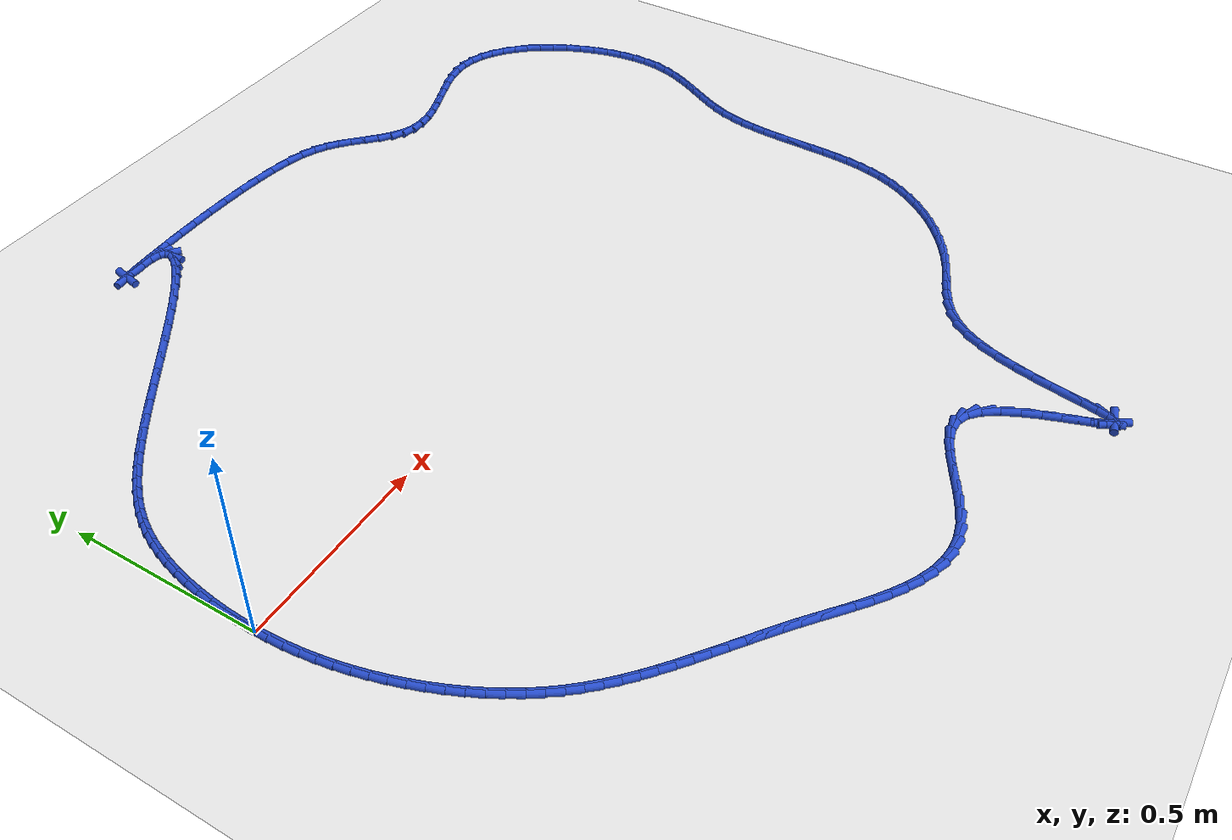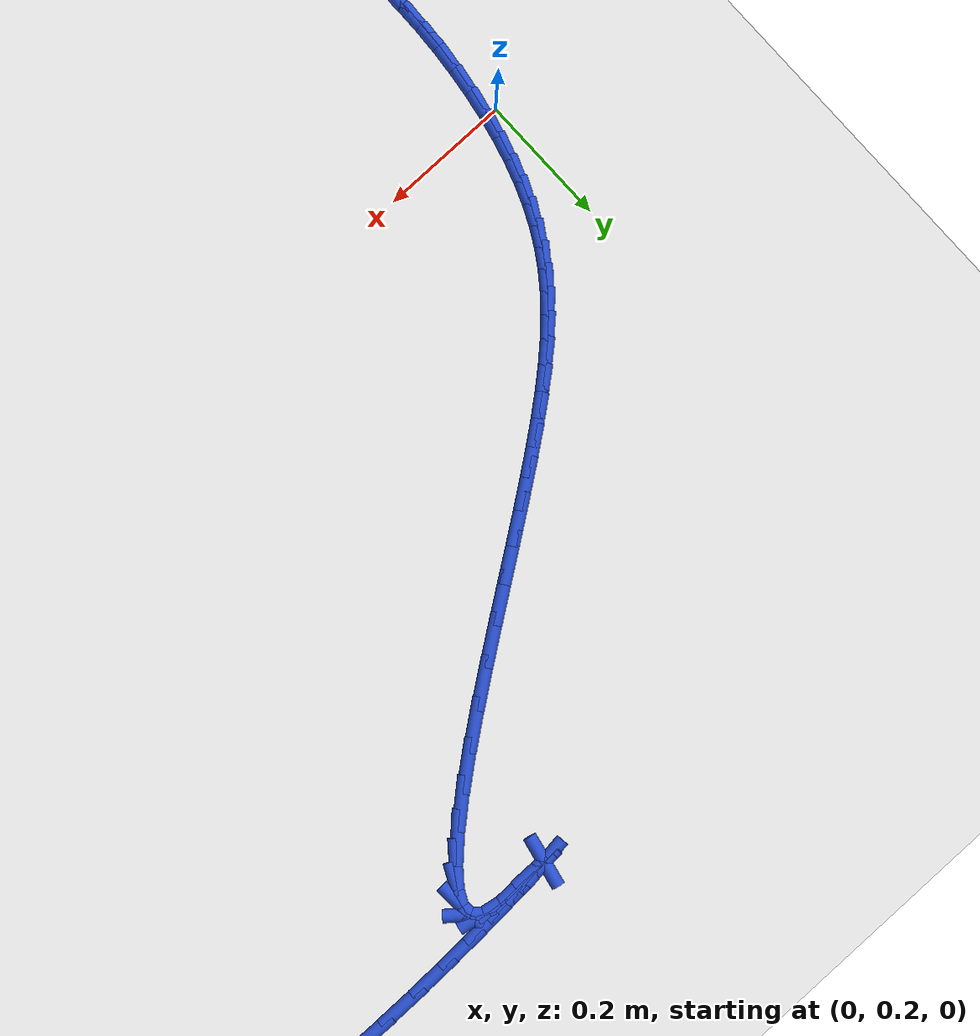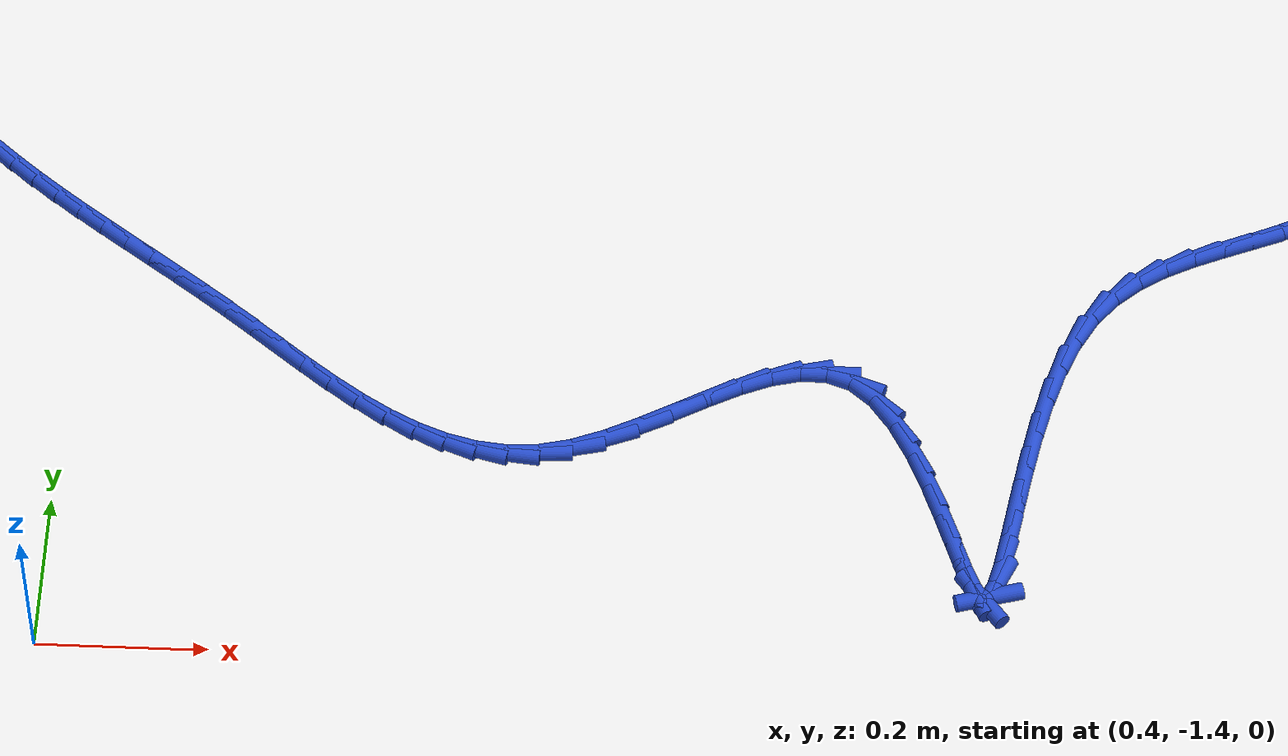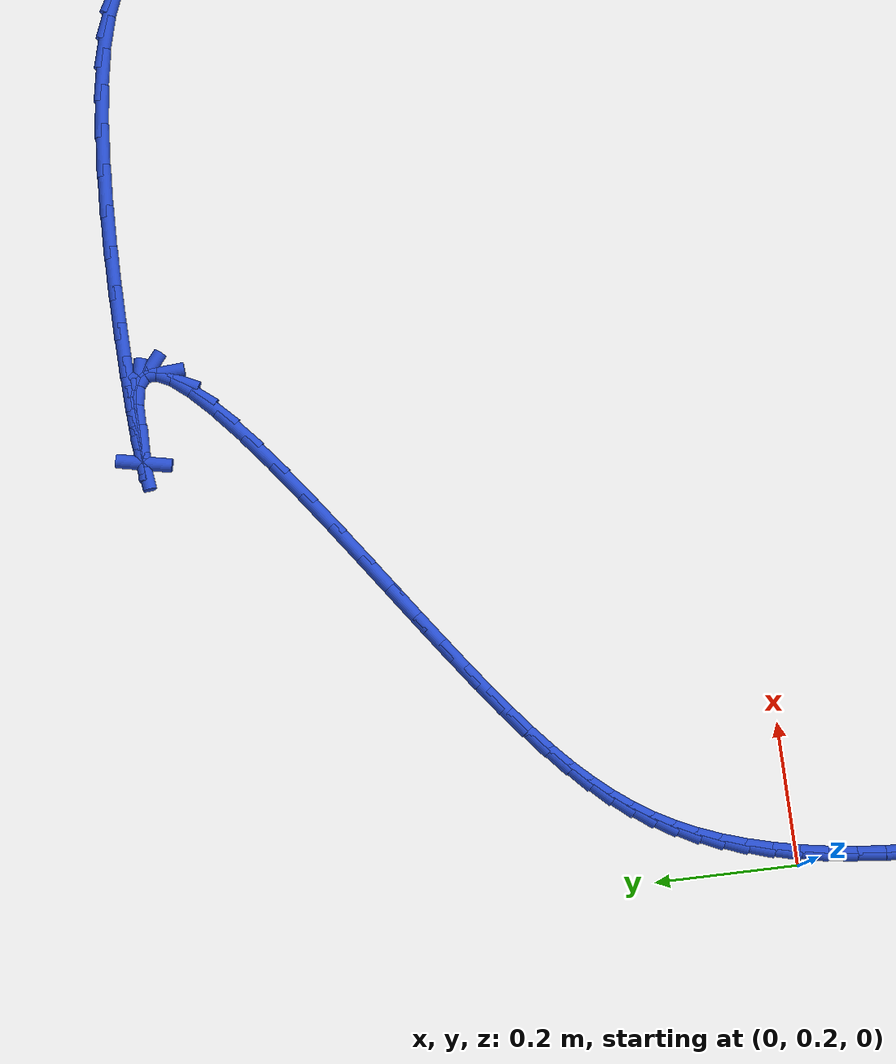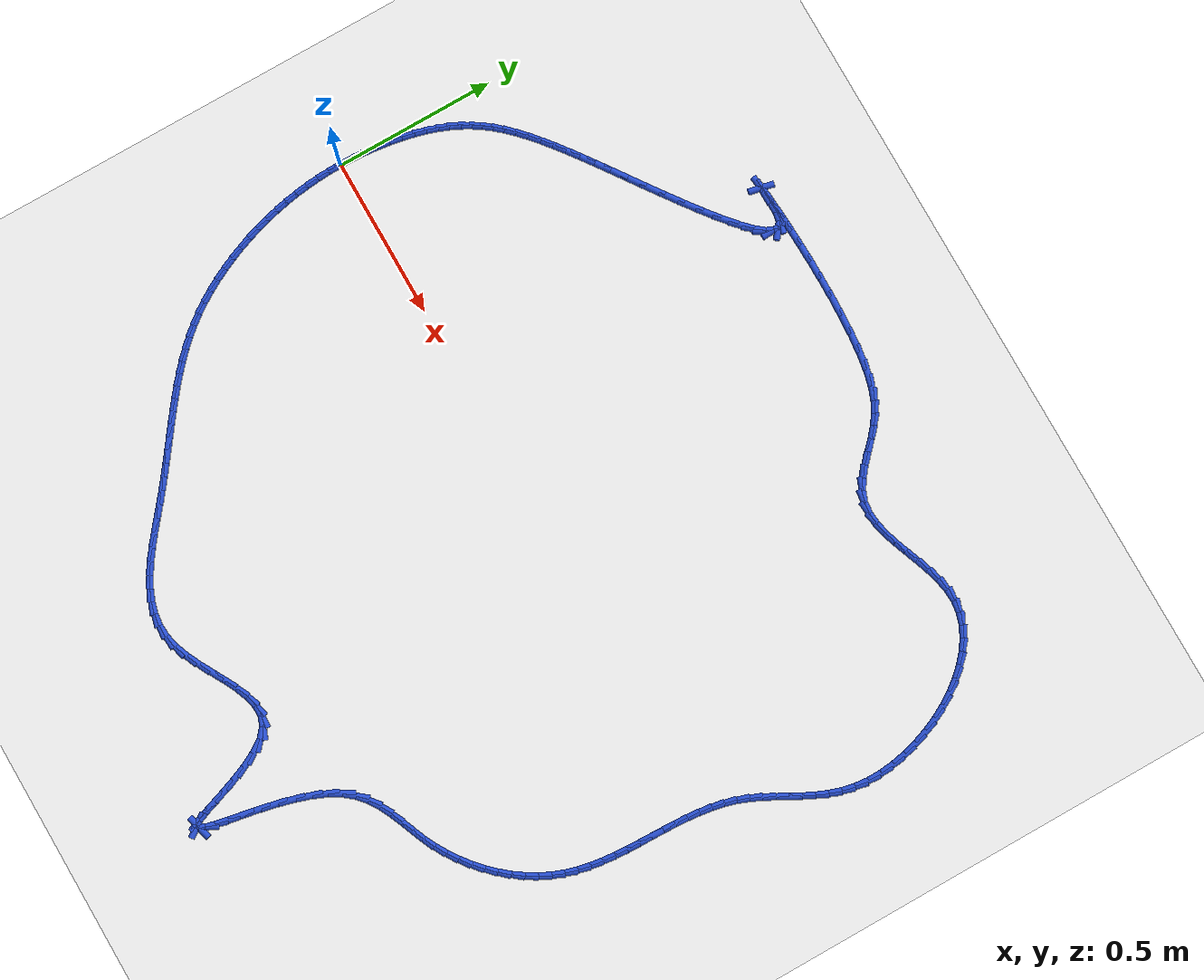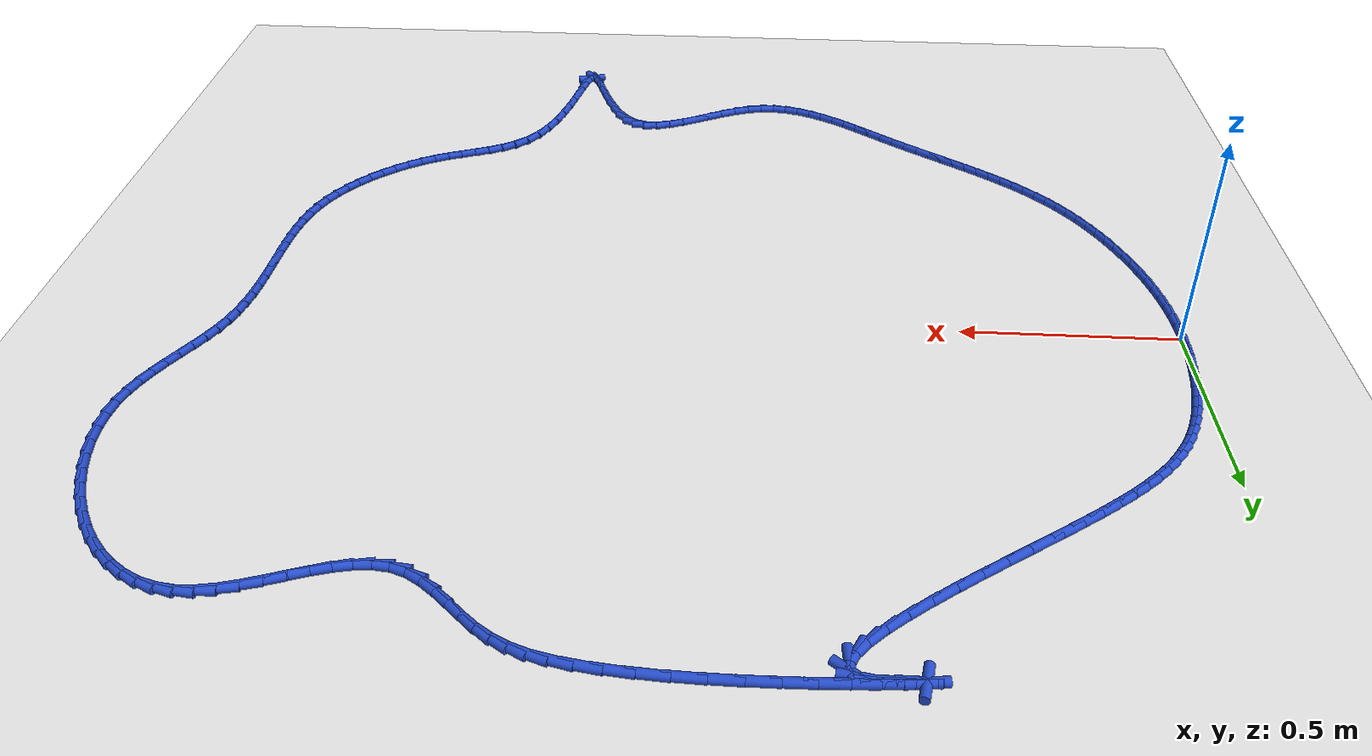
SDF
<sdf version="1.6">
 <world name="default">
  <light name="sun" type="directional">
   <pose>0 0 10 0 -0 0</pose>
   <diffuse>0.8 0.8 0.8 1</diffuse>
   <specular>0.2 0.2 0.2 1</specular>
   <attenuation>
    <range>1000</range>
    <constant>0.9</constant>
    <linear>0.01</linear>
    <quadratic>0.001</quadratic>
   </attenuation>
   <direction>-0.5 0.1 -0.9</direction>
  </light>
  <model name="ground_plane">
   <static>1</static>
   <link name="link">
    <collision name="collision">
     <geometry><plane><normal>0 0 1</normal><size>100 100</size></plane></geometry>
     <surface><friction><ode><mu>100</mu><mu2>50</mu2></ode></friction></surface>
    </collision>
    <visual name="visual">
     <cast_shadows>0</cast_shadows>
     <geometry><plane><normal>0 0 1</normal><size>100 100</size></plane></geometry>
     <material>
      <script><uri>file://media/materials/scripts/gazebo.material</uri><name>Gazebo/WhiteGlow</name></script>
     </material>
    </visual>
   </link>
  </model>
  <gravity>0 0 -9.8</gravity>
  <magnetic_field>6e-06 2.3e-05 -4.2e-05</magnetic_field>
  <atmosphere type="adiabatic"/>
  <physics name="default_physics" default="0" type="ode">
   <max_step_size>0.001</max_step_size>
   <real_time_factor>1</real_time_factor>
   <real_time_update_rate>1000</real_time_update_rate>
  </physics>
  <scene><ambient>0.4 0.4 0.4 1</ambient><background>0.7 0.7 0.7 1</background><shadows>1</shadows></scene>
  <spherical_coordinates>
   <surface_model>EARTH_WGS84</surface_model>
   <latitude_deg>0</latitude_deg>
   <longitude_deg>0</longitude_deg>
   <elevation>0</elevation>
   <heading_deg>0</heading_deg>
  </spherical_coordinates>
  <model name="line">
   <link name="link_0">
    <pose>1.0408340855860843e-17 -5.551115123125783e-17 0.01 0 1.57 1.553180485187353</pose>
    <collision name="collision">
     <geometry><cylinder><radius>0.01</radius><length>0.08</length></cylinder></geometry>
    </collision>
    <visual name="visual">
     <material>
      <script><name>Gazebo/Blue</name><uri>file://media/materials/scripts/gazebo.material</uri></script>
     </material>
     <geometry><cylinder><radius>0.01</radius><length>0.08</length></cylinder></geometry>
    </visual>
   </link>
   <link name="link_1">
    <pose>0.0006947978671462665 0.03943757055368453 0.01 0 1.57 1.5161483572995698</pose>
    <collision name="collision">
     <geometry><cylinder><radius>0.01</radius><length>0.08</length></cylinder></geometry>
    </collision>
    <visual name="visual">
     <material>
      <script><name>Gazebo/Blue</name><uri>file://media/materials/scripts/gazebo.material</uri></script>
     </material>
     <geometry><cylinder><radius>0.01</radius><length>0.08</length></cylinder></geometry>
    </visual>
   </link>
   <link name="link_2">
    <pose>0.002861904546496357 0.07905384517186925 0.01 0 1.57 1.4789762295758846</pose>
    <collision name="collision">
     <geometry><cylinder><radius>0.01</radius><length>0.08</length></cylinder></geometry>
    </collision>
    <visual name="visual">
     <material>
      <script><name>Gazebo/Blue</name><uri>file://media/materials/scripts/gazebo.material</uri></script>
     </material>
     <geometry><cylinder><radius>0.01</radius><length>0.08</length></cylinder></geometry>
    </visual>
   </link>
   <link name="link_3">
    <pose>0.00649612071170814 0.11852229767331711 0.01 0 1.57 1.440843181561353</pose>
    <collision name="collision">
     <geometry><cylinder><radius>0.01</radius><length>0.08</length></cylinder></geometry>
    </collision>
    <visual name="visual">
     <material>
      <script><name>Gazebo/Blue</name><uri>file://media/materials/scripts/gazebo.material</uri></script>
     </material>
     <geometry><cylinder><radius>0.01</radius><length>0.08</length></cylinder></geometry>
    </visual>
   </link>
   <link name="link_4">
    <pose>0.011592247036439475 0.15751640187679114 0.01 0 1.57 1.4008800360170088</pose>
    <collision name="collision">
     <geometry><cylinder><radius>0.01</radius><length>0.08</length></cylinder></geometry>
    </collision>
    <visual name="visual">
     <material>
      <script><name>Gazebo/Blue</name><uri>file://media/materials/scripts/gazebo.material</uri></script>
     </material>
     <geometry><cylinder><radius>0.01</radius><length>0.08</length></cylinder></geometry>
    </visual>
   </link>
   <link name="link_5">
    <pose>0.018145084194348203 0.1957096316010543 0.01 0 1.57 1.3581127591257378</pose>
    <collision name="collision">
     <geometry><cylinder><radius>0.01</radius><length>0.08</length></cylinder></geometry>
    </collision>
    <visual name="visual">
     <material>
      <script><name>Gazebo/Blue</name><uri>file://media/materials/scripts/gazebo.material</uri></script>
     </material>
     <geometry><cylinder><radius>0.01</radius><length>0.08</length></cylinder></geometry>
    </visual>
   </link>
   <link name="link_6">
    <pose>0.026149432859092207 0.23277546066486973 0.01 0 1.57 1.3113962401348565</pose>
    <collision name="collision">
     <geometry><cylinder><radius>0.01</radius><length>0.08</length></cylinder></geometry>
    </collision>
    <visual name="visual">
     <material>
      <script><name>Gazebo/Blue</name><uri>file://media/materials/scripts/gazebo.material</uri></script>
     </material>
     <geometry><cylinder><radius>0.01</radius><length>0.08</length></cylinder></geometry>
    </visual>
   </link>
   <link name="link_7">
    <pose>0.03560009370432934 0.26838736288700044 0.01 0 1.57 1.2593325169538567</pose>
    <collision name="collision">
     <geometry><cylinder><radius>0.01</radius><length>0.08</length></cylinder></geometry>
    </collision>
    <visual name="visual">
     <material>
      <script><name>Gazebo/Blue</name><uri>file://media/materials/scripts/gazebo.material</uri></script>
     </material>
     <geometry><cylinder><radius>0.01</radius><length>0.08</length></cylinder></geometry>
    </visual>
   </link>
   <link name="link_8">
    <pose>0.04649186740371744 0.30221881208620927 0.01 0 1.57 1.2003665097344187</pose>
    <collision name="collision">
     <geometry><cylinder><radius>0.01</radius><length>0.08</length></cylinder></geometry>
    </collision>
    <visual name="visual">
     <material>
      <script><name>Gazebo/Blue</name><uri>file://media/materials/scripts/gazebo.material</uri></script>
     </material>
     <geometry><cylinder><radius>0.01</radius><length>0.08</length></cylinder></geometry>
    </visual>
   </link>
   <link name="link_9">
    <pose>0.0588332389268023 0.3339971721542838 0.01 0 1.57 1.1350544345884321</pose>
    <collision name="collision">
     <geometry><cylinder><radius>0.01</radius><length>0.08</length></cylinder></geometry>
    </collision>
    <visual name="visual">
     <material>
      <script><name>Gazebo/Blue</name><uri>file://media/materials/scripts/gazebo.material</uri></script>
     </material>
     <geometry><cylinder><radius>0.01</radius><length>0.08</length></cylinder></geometry>
    </visual>
   </link>
   <link name="link_10">
    <pose>0.0727366241320405 0.36385909681704937 0.01 0 1.57 1.0658637802430917</pose>
    <collision name="collision">
     <geometry><cylinder><radius>0.01</radius><length>0.08</length></cylinder></geometry>
    </collision>
    <visual name="visual">
     <material>
      <script><name>Gazebo/Blue</name><uri>file://media/materials/scripts/gazebo.material</uri></script>
     </material>
     <geometry><cylinder><radius>0.01</radius><length>0.08</length></cylinder></geometry>
    </visual>
   </link>
   <link name="link_11">
    <pose>0.08836213779160033 0.39212908270903224 0.01 0 1.57 0.9955748882761528</pose>
    <collision name="collision">
     <geometry><cylinder><radius>0.01</radius><length>0.08</length></cylinder></geometry>
    </collision>
    <visual name="visual">
     <material>
      <script><name>Gazebo/Blue</name><uri>file://media/materials/scripts/gazebo.material</uri></script>
     </material>
     <geometry><cylinder><radius>0.01</radius><length>0.08</length></cylinder></geometry>
    </visual>
   </link>
   <link name="link_12">
    <pose>0.10587014466901742 0.4191326109548012 0.01 0 1.57 0.9271982014820962</pose>
    <collision name="collision">
     <geometry><cylinder><radius>0.01</radius><length>0.08</length></cylinder></geometry>
    </collision>
    <visual name="visual">
     <material>
      <script><name>Gazebo/Blue</name><uri>file://media/materials/scripts/gazebo.material</uri></script>
     </material>
     <geometry><cylinder><radius>0.01</radius><length>0.08</length></cylinder></geometry>
    </visual>
   </link>
   <link name="link_13">
    <pose>0.1254210095278276 0.44519516267892545 0.01 0 1.57 0.8634780714453385</pose>
    <collision name="collision">
     <geometry><cylinder><radius>0.01</radius><length>0.08</length></cylinder></geometry>
    </collision>
    <visual name="visual">
     <material>
      <script><name>Gazebo/Blue</name><uri>file://media/materials/scripts/gazebo.material</uri></script>
     </material>
     <geometry><cylinder><radius>0.01</radius><length>0.08</length></cylinder></geometry>
    </visual>
   </link>
   <link name="link_14">
    <pose>0.1471750971315665 0.4706422190059742 0.01 0 1.57 0.8064883470756027</pose>
    <collision name="collision">
     <geometry><cylinder><radius>0.01</radius><length>0.08</length></cylinder></geometry>
    </collision>
    <visual name="visual">
     <material>
      <script><name>Gazebo/Blue</name><uri>file://media/materials/scripts/gazebo.material</uri></script>
     </material>
     <geometry><cylinder><radius>0.01</radius><length>0.08</length></cylinder></geometry>
    </visual>
   </link>
   <link name="link_15">
    <pose>0.17129277224376993 0.4957992610605165 0.01 0 1.57 0.7574486069481038</pose>
    <collision name="collision">
     <geometry><cylinder><radius>0.01</radius><length>0.08</length></cylinder></geometry>
    </collision>
    <visual name="visual">
     <material>
      <script><name>Gazebo/Blue</name><uri>file://media/materials/scripts/gazebo.material</uri></script>
     </material>
     <geometry><cylinder><radius>0.01</radius><length>0.08</length></cylinder></geometry>
    </visual>
   </link>
   <link name="link_16">
    <pose>0.19793439962797374 0.520991769967122 0.01 0 1.57 0.7167647218897261</pose>
    <collision name="collision">
     <geometry><cylinder><radius>0.01</radius><length>0.08</length></cylinder></geometry>
    </collision>
    <visual name="visual">
     <material>
      <script><name>Gazebo/Blue</name><uri>file://media/materials/scripts/gazebo.material</uri></script>
     </material>
     <geometry><cylinder><radius>0.01</radius><length>0.08</length></cylinder></geometry>
    </visual>
   </link>
   <link name="link_17">
    <pose>0.22726034404771345 0.5465452268503592 0.01 0 1.57 0.684209451691147</pose>
    <collision name="collision">
     <geometry><cylinder><radius>0.01</radius><length>0.08</length></cylinder></geometry>
    </collision>
    <visual name="visual">
     <material>
      <script><name>Gazebo/Blue</name><uri>file://media/materials/scripts/gazebo.material</uri></script>
     </material>
     <geometry><cylinder><radius>0.01</radius><length>0.08</length></cylinder></geometry>
    </visual>
   </link>
   <link name="link_18">
    <pose>0.25943097026652484 0.5727851128347976 0.01 0 1.57 0.6591439779168842</pose>
    <collision name="collision">
     <geometry><cylinder><radius>0.01</radius><length>0.08</length></cylinder></geometry>
    </collision>
    <visual name="visual">
     <material>
      <script><name>Gazebo/Blue</name><uri>file://media/materials/scripts/gazebo.material</uri></script>
     </material>
     <geometry><cylinder><radius>0.01</radius><length>0.08</length></cylinder></geometry>
    </visual>
   </link>
   <link name="link_19">
    <pose>0.2946066430479437 0.6000369090450062 0.01 0 1.57 0.640713942559475</pose>
    <collision name="collision">
     <geometry><cylinder><radius>0.01</radius><length>0.08</length></cylinder></geometry>
    </collision>
    <visual name="visual">
     <material>
      <script><name>Gazebo/Blue</name><uri>file://media/materials/scripts/gazebo.material</uri></script>
     </material>
     <geometry><cylinder><radius>0.01</radius><length>0.08</length></cylinder></geometry>
    </visual>
   </link>
   <link name="link_20">
    <pose>0.3329477271555058 0.6286260966055542 0.01 0 1.57 0.6279935170746894</pose>
    <collision name="collision">
     <geometry><cylinder><radius>0.01</radius><length>0.08</length></cylinder></geometry>
    </collision>
    <visual name="visual">
     <material>
      <script><name>Gazebo/Blue</name><uri>file://media/materials/scripts/gazebo.material</uri></script>
     </material>
     <geometry><cylinder><radius>0.01</radius><length>0.08</length></cylinder></geometry>
    </visual>
   </link>
   <link name="link_21">
    <pose>0.3746145873527467 0.6588781566410109 0.01 0 1.57 0.6200981784517441</pose>
    <collision name="collision">
     <geometry><cylinder><radius>0.01</radius><length>0.08</length></cylinder></geometry>
    </collision>
    <visual name="visual">
     <material>
      <script><name>Gazebo/Blue</name><uri>file://media/materials/scripts/gazebo.material</uri></script>
     </material>
     <geometry><cylinder><radius>0.01</radius><length>0.08</length></cylinder></geometry>
    </visual>
   </link>
   <link name="link_22">
    <pose>0.4197524175502172 0.6911091508082289 0.01 0 1.57 0.616970095076636</pose>
    <collision name="collision">
     <geometry><cylinder><radius>0.01</radius><length>0.08</length></cylinder></geometry>
    </collision>
    <visual name="visual">
     <material>
      <script><name>Gazebo/Blue</name><uri>file://media/materials/scripts/gazebo.material</uri></script>
     </material>
     <geometry><cylinder><radius>0.01</radius><length>0.08</length></cylinder></geometry>
    </visual>
   </link>
   <link name="link_23">
    <pose>0.4678574924936432 0.7252322317694506 0.01 0 1.57 0.6187817957627876</pose>
    <collision name="collision">
     <geometry><cylinder><radius>0.01</radius><length>0.08</length></cylinder></geometry>
    </collision>
    <visual name="visual">
     <material>
      <script><name>Gazebo/Blue</name><uri>file://media/materials/scripts/gazebo.material</uri></script>
     </material>
     <geometry><cylinder><radius>0.01</radius><length>0.08</length></cylinder></geometry>
    </visual>
   </link>
   <link name="link_24">
    <pose>0.5175472056928802 0.7606148614840983 0.01 0 1.57 0.6252613970484798</pose>
    <collision name="collision">
     <geometry><cylinder><radius>0.01</radius><length>0.08</length></cylinder></geometry>
    </collision>
    <visual name="visual">
     <material>
      <script><name>Gazebo/Blue</name><uri>file://media/materials/scripts/gazebo.material</uri></script>
     </material>
     <geometry><cylinder><radius>0.01</radius><length>0.08</length></cylinder></geometry>
    </visual>
   </link>
   <link name="link_25">
    <pose>0.5673764566420325 0.7965856998505363 0.01 0 1.57 0.6368063150271496</pose>
    <collision name="collision">
     <geometry><cylinder><radius>0.01</radius><length>0.08</length></cylinder></geometry>
    </collision>
    <visual name="visual">
     <material>
      <script><name>Gazebo/Blue</name><uri>file://media/materials/scripts/gazebo.material</uri></script>
     </material>
     <geometry><cylinder><radius>0.01</radius><length>0.08</length></cylinder></geometry>
    </visual>
   </link>
   <link name="link_26">
    <pose>0.6159001448352044 0.8324734067671283 0.01 0 1.57 0.6546408835094804</pose>
    <collision name="collision">
     <geometry><cylinder><radius>0.01</radius><length>0.08</length></cylinder></geometry>
    </collision>
    <visual name="visual">
     <material>
      <script><name>Gazebo/Blue</name><uri>file://media/materials/scripts/gazebo.material</uri></script>
     </material>
     <geometry><cylinder><radius>0.01</radius><length>0.08</length></cylinder></geometry>
    </visual>
   </link>
   <link name="link_27">
    <pose>0.6616731697665004 0.8676066421322389 0.01 0 1.57 0.6812420758496388</pose>
    <collision name="collision">
     <geometry><cylinder><radius>0.01</radius><length>0.08</length></cylinder></geometry>
    </collision>
    <visual name="visual">
     <material>
      <script><name>Gazebo/Blue</name><uri>file://media/materials/scripts/gazebo.material</uri></script>
     </material>
     <geometry><cylinder><radius>0.01</radius><length>0.08</length></cylinder></geometry>
    </visual>
   </link>
   <link name="link_28">
    <pose>0.7032504309300246 0.9013140658442317 0.01 0 1.57 0.7214390616236003</pose>
    <collision name="collision">
     <geometry><cylinder><radius>0.01</radius><length>0.08</length></cylinder></geometry>
    </collision>
    <visual name="visual">
     <material>
      <script><name>Gazebo/Blue</name><uri>file://media/materials/scripts/gazebo.material</uri></script>
     </material>
     <geometry><cylinder><radius>0.01</radius><length>0.08</length></cylinder></geometry>
    </visual>
   </link>
   <link name="link_29">
    <pose>0.7391868278198812 0.9329243378014703 0.01 0 1.57 0.7852481949866682</pose>
    <collision name="collision">
     <geometry><cylinder><radius>0.01</radius><length>0.08</length></cylinder></geometry>
    </collision>
    <visual name="visual">
     <material>
      <script><name>Gazebo/Blue</name><uri>file://media/materials/scripts/gazebo.material</uri></script>
     </material>
     <geometry><cylinder><radius>0.01</radius><length>0.08</length></cylinder></geometry>
    </visual>
   </link>
   <link name="link_30">
    <pose>0.7680372599301752 0.9617661179023198 0.01 0 1.57 0.8961079967658859</pose>
    <collision name="collision">
     <geometry><cylinder><radius>0.01</radius><length>0.08</length></cylinder></geometry>
    </collision>
    <visual name="visual">
     <material>
      <script><name>Gazebo/Blue</name><uri>file://media/materials/scripts/gazebo.material</uri></script>
     </material>
     <geometry><cylinder><radius>0.01</radius><length>0.08</length></cylinder></geometry>
    </visual>
   </link>
   <link name="link_31">
    <pose>0.7883566267550107 0.9871680660451438 0.01 0 1.57 1.118567717611893</pose>
    <collision name="collision">
     <geometry><cylinder><radius>0.01</radius><length>0.08</length></cylinder></geometry>
    </collision>
    <visual name="visual">
     <material>
      <script><name>Gazebo/Blue</name><uri>file://media/materials/scripts/gazebo.material</uri></script>
     </material>
     <geometry><cylinder><radius>0.01</radius><length>0.08</length></cylinder></geometry>
    </visual>
   </link>
   <link name="link_32">
    <pose>0.7986998277884919 1.0084588421283063 0.01 0 1.57 -1.5055843432101452</pose>
    <collision name="collision">
     <geometry><cylinder><radius>0.01</radius><length>0.08</length></cylinder></geometry>
    </collision>
    <visual name="visual">
     <material>
      <script><name>Gazebo/Blue</name><uri>file://media/materials/scripts/gazebo.material</uri></script>
     </material>
     <geometry><cylinder><radius>0.01</radius><length>0.08</length></cylinder></geometry>
    </visual>
   </link>
   <link name="link_33">
    <pose>0.7976217625247232 1.0249671060501713 0.01 0 1.57 -0.6703029265155137</pose>
    <collision name="collision">
     <geometry><cylinder><radius>0.01</radius><length>0.08</length></cylinder></geometry>
    </collision>
    <visual name="visual">
     <material>
      <script><name>Gazebo/Blue</name><uri>file://media/materials/scripts/gazebo.material</uri></script>
     </material>
     <geometry><cylinder><radius>0.01</radius><length>0.08</length></cylinder></geometry>
    </visual>
   </link>
   <link name="link_34">
    <pose>0.7836773304578089 1.036021517709103 0.01 0 1.57 -0.1727272816999848</pose>
    <collision name="collision">
     <geometry><cylinder><radius>0.01</radius><length>0.08</length></cylinder></geometry>
    </collision>
    <visual name="visual">
     <material>
      <script><name>Gazebo/Blue</name><uri>file://media/materials/scripts/gazebo.material</uri></script>
     </material>
     <geometry><cylinder><radius>0.01</radius><length>0.08</length></cylinder></geometry>
    </visual>
   </link>
   <link name="link_35">
    <pose>0.7554225045401322 1.0409510181812782 0.01 0 1.57 0.013539274539179837</pose>
    <collision name="collision">
     <geometry><cylinder><radius>0.01</radius><length>0.08</length></cylinder></geometry>
    </collision>
    <visual name="visual">
     <material>
      <script><name>Gazebo/Blue</name><uri>file://media/materials/scripts/gazebo.material</uri></script>
     </material>
     <geometry><cylinder><radius>0.01</radius><length>0.08</length></cylinder></geometry>
    </visual>
   </link>
   <link name="link_36">
    <pose>0.7165283898204996 1.040424387904529 0.01 0 1.57 0.04062246191361496</pose>
    <collision name="collision">
     <geometry><cylinder><radius>0.01</radius><length>0.08</length></cylinder></geometry>
    </collision>
    <visual name="visual">
     <material>
      <script><name>Gazebo/Blue</name><uri>file://media/materials/scripts/gazebo.material</uri></script>
     </material>
     <geometry><cylinder><radius>0.01</radius><length>0.08</length></cylinder></geometry>
    </visual>
   </link>
   <link name="link_37">
    <pose>0.6861410985516151 1.0391893018743115 0.01 0 1.57 -0.0012549470230298768</pose>
    <collision name="collision">
     <geometry><cylinder><radius>0.01</radius><length>0.08</length></cylinder></geometry>
    </collision>
    <visual name="visual">
     <material>
      <script><name>Gazebo/Blue</name><uri>file://media/materials/scripts/gazebo.material</uri></script>
     </material>
     <geometry><cylinder><radius>0.01</radius><length>0.08</length></cylinder></geometry>
    </visual>
   </link>
   <link name="link_38">
    <pose>0.6717681432782258 1.0392073391812129 0.01 0 1.57 1.3668447132955854</pose>
    <collision name="collision">
     <geometry><cylinder><radius>0.01</radius><length>0.08</length></cylinder></geometry>
    </collision>
    <visual name="visual">
     <material>
      <script><name>Gazebo/Blue</name><uri>file://media/materials/scripts/gazebo.material</uri></script>
     </material>
     <geometry><cylinder><radius>0.01</radius><length>0.08</length></cylinder></geometry>
    </visual>
   </link>
   <link name="link_39">
    <pose>0.6719848823333776 1.0402552618068033 0.01 0 1.57 0.13680672893093607</pose>
    <collision name="collision">
     <geometry><cylinder><radius>0.01</radius><length>0.08</length></cylinder></geometry>
    </collision>
    <visual name="visual">
     <material>
      <script><name>Gazebo/Blue</name><uri>file://media/materials/scripts/gazebo.material</uri></script>
     </material>
     <geometry><cylinder><radius>0.01</radius><length>0.08</length></cylinder></geometry>
    </visual>
   </link>
   <link name="link_40">
    <pose>0.6852512454742516 1.0420815977454811 0.01 0 1.57 0.09469835093375538</pose>
    <collision name="collision">
     <geometry><cylinder><radius>0.01</radius><length>0.08</length></cylinder></geometry>
    </collision>
    <visual name="visual">
     <material>
      <script><name>Gazebo/Blue</name><uri>file://media/materials/scripts/gazebo.material</uri></script>
     </material>
     <geometry><cylinder><radius>0.01</radius><length>0.08</length></cylinder></geometry>
    </visual>
   </link>
   <link name="link_41">
    <pose>0.710027162458029 1.0444348749916466 0.01 0 1.57 0.07551353488330204</pose>
    <collision name="collision">
     <geometry><cylinder><radius>0.01</radius><length>0.08</length></cylinder></geometry>
    </collision>
    <visual name="visual">
     <material>
      <script><name>Gazebo/Blue</name><uri>file://media/materials/scripts/gazebo.material</uri></script>
     </material>
     <geometry><cylinder><radius>0.01</radius><length>0.08</length></cylinder></geometry>
    </visual>
   </link>
   <link name="link_42">
    <pose>0.7447725630418902 1.0470636215396982 0.01 0 1.57 0.061364786768981265</pose>
    <collision name="collision">
     <geometry><cylinder><radius>0.01</radius><length>0.08</length></cylinder></geometry>
    </collision>
    <visual name="visual">
     <material>
      <script><name>Gazebo/Blue</name><uri>file://media/materials/scripts/gazebo.material</uri></script>
     </material>
     <geometry><cylinder><radius>0.01</radius><length>0.08</length></cylinder></geometry>
    </visual>
   </link>
   <link name="link_43">
    <pose>0.7879473769830165 1.0497163653840356 0.01 0 1.57 0.048405381832603116</pose>
    <collision name="collision">
     <geometry><cylinder><radius>0.01</radius><length>0.08</length></cylinder></geometry>
    </collision>
    <visual name="visual">
     <material>
      <script><name>Gazebo/Blue</name><uri>file://media/materials/scripts/gazebo.material</uri></script>
     </material>
     <geometry><cylinder><radius>0.01</radius><length>0.08</length></cylinder></geometry>
    </visual>
   </link>
   <link name="link_44">
    <pose>0.8380115340385887 1.0521416345190573 0.01 0 1.57 0.035109226056950896</pose>
    <collision name="collision">
     <geometry><cylinder><radius>0.01</radius><length>0.08</length></cylinder></geometry>
    </collision>
    <visual name="visual">
     <material>
      <script><name>Gazebo/Blue</name><uri>file://media/materials/scripts/gazebo.material</uri></script>
     </material>
     <geometry><cylinder><radius>0.01</radius><length>0.08</length></cylinder></geometry>
    </visual>
   </link>
   <link name="link_45">
    <pose>0.8934249639657881 1.054087956939163 0.01 0 1.57 0.020528180627371145</pose>
    <collision name="collision">
     <geometry><cylinder><radius>0.01</radius><length>0.08</length></cylinder></geometry>
    </collision>
    <visual name="visual">
     <material>
      <script><name>Gazebo/Blue</name><uri>file://media/materials/scripts/gazebo.material</uri></script>
     </material>
     <geometry><cylinder><radius>0.01</radius><length>0.08</length></cylinder></geometry>
    </visual>
   </link>
   <link name="link_46">
    <pose>0.9526475965217949 1.0553038606387521 0.01 0 1.57 0.0038055802105734274</pose>
    <collision name="collision">
     <geometry><cylinder><radius>0.01</radius><length>0.08</length></cylinder></geometry>
    </collision>
    <visual name="visual">
     <material>
      <script><name>Gazebo/Blue</name><uri>file://media/materials/scripts/gazebo.material</uri></script>
     </material>
     <geometry><cylinder><radius>0.01</radius><length>0.08</length></cylinder></geometry>
    </visual>
   </link>
   <link name="link_47">
    <pose>1.0141393614637901 1.0555378736122227 0.01 0 1.57 -0.01605995749989276</pose>
    <collision name="collision">
     <geometry><cylinder><radius>0.01</radius><length>0.08</length></cylinder></geometry>
    </collision>
    <visual name="visual">
     <material>
      <script><name>Gazebo/Blue</name><uri>file://media/materials/scripts/gazebo.material</uri></script>
     </material>
     <geometry><cylinder><radius>0.01</radius><length>0.08</length></cylinder></geometry>
    </visual>
   </link>
   <link name="link_48">
    <pose>1.0763601885489549 1.054538523853975 0.01 0 1.57 -0.040430517750504186</pose>
    <collision name="collision">
     <geometry><cylinder><radius>0.01</radius><length>0.08</length></cylinder></geometry>
    </collision>
    <visual name="visual">
     <material>
      <script><name>Gazebo/Blue</name><uri>file://media/materials/scripts/gazebo.material</uri></script>
     </material>
     <geometry><cylinder><radius>0.01</radius><length>0.08</length></cylinder></geometry>
    </visual>
   </link>
   <link name="link_49">
    <pose>1.1377700075344708 1.0520543393584083 0.01 0 1.57 -0.07134132187872208</pose>
    <collision name="collision">
     <geometry><cylinder><radius>0.01</radius><length>0.08</length></cylinder></geometry>
    </collision>
    <visual name="visual">
     <material>
      <script><name>Gazebo/Blue</name><uri>file://media/materials/scripts/gazebo.material</uri></script>
     </material>
     <geometry><cylinder><radius>0.01</radius><length>0.08</length></cylinder></geometry>
    </visual>
   </link>
   <link name="link_50">
    <pose>1.1968287481775177 1.047833848119921 0.01 0 1.57 -0.11206325662532374</pose>
    <collision name="collision">
     <geometry><cylinder><radius>0.01</radius><length>0.08</length></cylinder></geometry>
    </collision>
    <visual name="visual">
     <material>
      <script><name>Gazebo/Blue</name><uri>file://media/materials/scripts/gazebo.material</uri></script>
     </material>
     <geometry><cylinder><radius>0.01</radius><length>0.08</length></cylinder></geometry>
    </visual>
   </link>
   <link name="link_51">
    <pose>1.2519963402352774 1.041625578132913 0.01 0 1.57 -0.16824041431538736</pose>
    <collision name="collision">
     <geometry><cylinder><radius>0.01</radius><length>0.08</length></cylinder></geometry>
    </collision>
    <visual name="visual">
     <material>
      <script><name>Gazebo/Blue</name><uri>file://media/materials/scripts/gazebo.material</uri></script>
     </material>
     <geometry><cylinder><radius>0.01</radius><length>0.08</length></cylinder></geometry>
    </visual>
   </link>
   <link name="link_52">
    <pose>1.30173271346493 1.0331780573917828 0.01 0 1.57 -0.24964533895977073</pose>
    <collision name="collision">
     <geometry><cylinder><radius>0.01</radius><length>0.08</length></cylinder></geometry>
    </collision>
    <visual name="visual">
     <material>
      <script><name>Gazebo/Blue</name><uri>file://media/materials/scripts/gazebo.material</uri></script>
     </material>
     <geometry><cylinder><radius>0.01</radius><length>0.08</length></cylinder></geometry>
    </visual>
   </link>
   <link name="link_53">
    <pose>1.3446758379282162 1.022229099277767 0.01 0 1.57 -0.35998212723259215</pose>
    <collision name="collision">
     <geometry><cylinder><radius>0.01</radius><length>0.08</length></cylinder></geometry>
    </collision>
    <visual name="visual">
     <material>
      <script><name>Gazebo/Blue</name><uri>file://media/materials/scripts/gazebo.material</uri></script>
     </material>
     <geometry><cylinder><radius>0.01</radius><length>0.08</length></cylinder></geometry>
    </visual>
   </link>
   <link name="link_54">
    <pose>1.3814214459663139 1.0083986974147134 0.01 0 1.57 -0.48775100203156085</pose>
    <collision name="collision">
     <geometry><cylinder><radius>0.01</radius><length>0.08</length></cylinder></geometry>
    </collision>
    <visual name="visual">
     <material>
      <script><name>Gazebo/Blue</name><uri>file://media/materials/scripts/gazebo.material</uri></script>
     </material>
     <geometry><cylinder><radius>0.01</radius><length>0.08</length></cylinder></geometry>
    </visual>
   </link>
   <link name="link_55">
    <pose>1.413777136583344 0.9912339142857912 0.01 0 1.57 -0.6129575581060966</pose>
    <collision name="collision">
     <geometry><cylinder><radius>0.01</radius><length>0.08</length></cylinder></geometry>
    </collision>
    <visual name="visual">
     <material>
      <script><name>Gazebo/Blue</name><uri>file://media/materials/scripts/gazebo.material</uri></script>
     </material>
     <geometry><cylinder><radius>0.01</radius><length>0.08</length></cylinder></geometry>
    </visual>
   </link>
   <link name="link_56">
    <pose>1.443568525797221 0.970280728095339 0.01 0 1.57 -0.711584287271909</pose>
    <collision name="collision">
     <geometry><cylinder><radius>0.01</radius><length>0.08</length></cylinder></geometry>
    </collision>
    <visual name="visual">
     <material>
      <script><name>Gazebo/Blue</name><uri>file://media/materials/scripts/gazebo.material</uri></script>
     </material>
     <geometry><cylinder><radius>0.01</radius><length>0.08</length></cylinder></geometry>
    </visual>
   </link>
   <link name="link_57">
    <pose>1.4724991946644577 0.945334183627276 0.01 0 1.57 -0.7575457044002362</pose>
    <collision name="collision">
     <geometry><cylinder><radius>0.01</radius><length>0.08</length></cylinder></geometry>
    </collision>
    <visual name="visual">
     <material>
      <script><name>Gazebo/Blue</name><uri>file://media/materials/scripts/gazebo.material</uri></script>
     </material>
     <geometry><cylinder><radius>0.01</radius><length>0.08</length></cylinder></geometry>
    </visual>
   </link>
   <link name="link_58">
    <pose>1.501373011101334 0.9180255902233212 0.01 0 1.57 -0.7499684025760196</pose>
    <collision name="collision">
     <geometry><cylinder><radius>0.01</radius><length>0.08</length></cylinder></geometry>
    </collision>
    <visual name="visual">
     <material>
      <script><name>Gazebo/Blue</name><uri>file://media/materials/scripts/gazebo.material</uri></script>
     </material>
     <geometry><cylinder><radius>0.01</radius><length>0.08</length></cylinder></geometry>
    </visual>
   </link>
   <link name="link_59">
    <pose>1.5305914487762449 0.8908075215400265 0.01 0 1.57 -0.6888449929496289</pose>
    <collision name="collision">
     <geometry><cylinder><radius>0.01</radius><length>0.08</length></cylinder></geometry>
    </collision>
    <visual name="visual">
     <material>
      <script><name>Gazebo/Blue</name><uri>file://media/materials/scripts/gazebo.material</uri></script>
     </material>
     <geometry><cylinder><radius>0.01</radius><length>0.08</length></cylinder></geometry>
    </visual>
   </link>
   <link name="link_60">
    <pose>1.5605541016255768 0.8661363876625933 0.01 0 1.57 -0.5638125483090682</pose>
    <collision name="collision">
     <geometry><cylinder><radius>0.01</radius><length>0.08</length></cylinder></geometry>
    </collision>
    <visual name="visual">
     <material>
      <script><name>Gazebo/Blue</name><uri>file://media/materials/scripts/gazebo.material</uri></script>
     </material>
     <geometry><cylinder><radius>0.01</radius><length>0.08</length></cylinder></geometry>
    </visual>
   </link>
   <link name="link_61">
    <pose>1.591660563585716 0.8464685986762215 0.01 0 1.57 -0.35891688800518856</pose>
    <collision name="collision">
     <geometry><cylinder><radius>0.01</radius><length>0.08</length></cylinder></geometry>
    </collision>
    <visual name="visual">
     <material>
      <script><name>Gazebo/Blue</name><uri>file://media/materials/scripts/gazebo.material</uri></script>
     </material>
     <geometry><cylinder><radius>0.01</radius><length>0.08</length></cylinder></geometry>
    </visual>
   </link>
   <link name="link_62">
    <pose>1.6243039983144294 0.8342218660952786 0.01 0 1.57 -0.11702031290534819</pose>
    <collision name="collision">
     <geometry><cylinder><radius>0.01</radius><length>0.08</length></cylinder></geometry>
    </collision>
    <visual name="visual">
     <material>
      <script><name>Gazebo/Blue</name><uri>file://media/materials/scripts/gazebo.material</uri></script>
     </material>
     <geometry><cylinder><radius>0.01</radius><length>0.08</length></cylinder></geometry>
    </visual>
   </link>
   <link name="link_63">
    <pose>1.6586076076627245 0.8301892228281101 0.01 0 1.57 0.0779850970648842</pose>
    <collision name="collision">
     <geometry><cylinder><radius>0.01</radius><length>0.08</length></cylinder></geometry>
    </collision>
    <visual name="visual">
     <material>
      <script><name>Gazebo/Blue</name><uri>file://media/materials/scripts/gazebo.material</uri></script>
     </material>
     <geometry><cylinder><radius>0.01</radius><length>0.08</length></cylinder></geometry>
    </visual>
   </link>
   <link name="link_64">
    <pose>1.6943318830750815 0.832980845457082 0.01 0 1.57 0.21549179162106377</pose>
    <collision name="collision">
     <geometry><cylinder><radius>0.01</radius><length>0.08</length></cylinder></geometry>
    </collision>
    <visual name="visual">
     <material>
      <script><name>Gazebo/Blue</name><uri>file://media/materials/scripts/gazebo.material</uri></script>
     </material>
     <geometry><cylinder><radius>0.01</radius><length>0.08</length></cylinder></geometry>
    </visual>
   </link>
   <link name="link_65">
    <pose>1.7312118273575963 0.8410535153640378 0.01 0 1.57 0.3030580675471703</pose>
    <collision name="collision">
     <geometry><cylinder><radius>0.01</radius><length>0.08</length></cylinder></geometry>
    </collision>
    <visual name="visual">
     <material>
      <script><name>Gazebo/Blue</name><uri>file://media/materials/scripts/gazebo.material</uri></script>
     </material>
     <geometry><cylinder><radius>0.01</radius><length>0.08</length></cylinder></geometry>
    </visual>
   </link>
   <link name="link_66">
    <pose>1.7689824433163641 0.8528640139308218 0.01 0 1.57 0.34975564579583357</pose>
    <collision name="collision">
     <geometry><cylinder><radius>0.01</radius><length>0.08</length></cylinder></geometry>
    </collision>
    <visual name="visual">
     <material>
      <script><name>Gazebo/Blue</name><uri>file://media/materials/scripts/gazebo.material</uri></script>
     </material>
     <geometry><cylinder><radius>0.01</radius><length>0.08</length></cylinder></geometry>
    </visual>
   </link>
   <link name="link_67">
    <pose>1.8073787337574805 0.8668691225392774 0.01 0 1.57 0.3615419262131408</pose>
    <collision name="collision">
     <geometry><cylinder><radius>0.01</radius><length>0.08</length></cylinder></geometry>
    </collision>
    <visual name="visual">
     <material>
      <script><name>Gazebo/Blue</name><uri>file://media/materials/scripts/gazebo.material</uri></script>
     </material>
     <geometry><cylinder><radius>0.01</radius><length>0.08</length></cylinder></geometry>
    </visual>
   </link>
   <link name="link_68">
    <pose>1.8461357014870414 0.8815256225712488 0.01 0 1.57 0.34048164826875305</pose>
    <collision name="collision">
     <geometry><cylinder><radius>0.01</radius><length>0.08</length></cylinder></geometry>
    </collision>
    <visual name="visual">
     <material>
      <script><name>Gazebo/Blue</name><uri>file://media/materials/scripts/gazebo.material</uri></script>
     </material>
     <geometry><cylinder><radius>0.01</radius><length>0.08</length></cylinder></geometry>
    </visual>
   </link>
   <link name="link_69">
    <pose>1.8849883493111417 0.8952902954085792 0.01 0 1.57 0.28491321692455995</pose>
    <collision name="collision">
     <geometry><cylinder><radius>0.01</radius><length>0.08</length></cylinder></geometry>
    </collision>
    <visual name="visual">
     <material>
      <script><name>Gazebo/Blue</name><uri>file://media/materials/scripts/gazebo.material</uri></script>
     </material>
     <geometry><cylinder><radius>0.01</radius><length>0.08</length></cylinder></geometry>
    </visual>
   </link>
   <link name="link_70">
    <pose>1.9236716800358782 0.906619922433113 0.01 0 1.57 0.1898819541309615</pose>
    <collision name="collision">
     <geometry><cylinder><radius>0.01</radius><length>0.08</length></cylinder></geometry>
    </collision>
    <visual name="visual">
     <material>
      <script><name>Gazebo/Blue</name><uri>file://media/materials/scripts/gazebo.material</uri></script>
     </material>
     <geometry><cylinder><radius>0.01</radius><length>0.08</length></cylinder></geometry>
    </visual>
   </link>
   <link name="link_71">
    <pose>1.961920696467345 0.9139712850266938 0.01 0 1.57 0.04869988583270662</pose>
    <collision name="collision">
     <geometry><cylinder><radius>0.01</radius><length>0.08</length></cylinder></geometry>
    </collision>
    <visual name="visual">
     <material>
      <script><name>Gazebo/Blue</name><uri>file://media/materials/scripts/gazebo.material</uri></script>
     </material>
     <geometry><cylinder><radius>0.01</radius><length>0.08</length></cylinder></geometry>
    </visual>
   </link>
   <link name="link_72">
    <pose>1.9994704064927342 0.9158013986607431 0.01 0 1.57 -0.12999805306448606</pose>
    <collision name="collision">
     <geometry><cylinder><radius>0.01</radius><length>0.08</length></cylinder></geometry>
    </collision>
    <visual name="visual">
     <material>
      <script><name>Gazebo/Blue</name><uri>file://media/materials/scripts/gazebo.material</uri></script>
     </material>
     <geometry><cylinder><radius>0.01</radius><length>0.08</length></cylinder></geometry>
    </visual>
   </link>
   <link name="link_73">
    <pose>2.036065582065469 0.9110171160206859 0.01 0 1.57 -0.303849990025133</pose>
    <collision name="collision">
     <geometry><cylinder><radius>0.01</radius><length>0.08</length></cylinder></geometry>
    </collision>
    <visual name="visual">
     <material>
      <script><name>Gazebo/Blue</name><uri>file://media/materials/scripts/gazebo.material</uri></script>
     </material>
     <geometry><cylinder><radius>0.01</radius><length>0.08</length></cylinder></geometry>
    </visual>
   </link>
   <link name="link_74">
    <pose>2.0714810999092403 0.8999122371626421 0.01 0 1.57 -0.4602779804719352</pose>
    <collision name="collision">
     <geometry><cylinder><radius>0.01</radius><length>0.08</length></cylinder></geometry>
    </collision>
    <visual name="visual">
     <material>
      <script><name>Gazebo/Blue</name><uri>file://media/materials/scripts/gazebo.material</uri></script>
     </material>
     <geometry><cylinder><radius>0.01</radius><length>0.08</length></cylinder></geometry>
    </visual>
   </link>
   <link name="link_75">
    <pose>2.1054976203205893 0.8830470153023335 0.01 0 1.57 -0.5979054581356953</pose>
    <collision name="collision">
     <geometry><cylinder><radius>0.01</radius><length>0.08</length></cylinder></geometry>
    </collision>
    <visual name="visual">
     <material>
      <script><name>Gazebo/Blue</name><uri>file://media/materials/scripts/gazebo.material</uri></script>
     </material>
     <geometry><cylinder><radius>0.01</radius><length>0.08</length></cylinder></geometry>
    </visual>
   </link>
   <link name="link_76">
    <pose>2.1378958035960567 0.8609817036554817 0.01 0 1.57 -0.7181755116216579</pose>
    <collision name="collision">
     <geometry><cylinder><radius>0.01</radius><length>0.08</length></cylinder></geometry>
    </collision>
    <visual name="visual">
     <material>
      <script><name>Gazebo/Blue</name><uri>file://media/materials/scripts/gazebo.material</uri></script>
     </material>
     <geometry><cylinder><radius>0.01</radius><length>0.08</length></cylinder></geometry>
    </visual>
   </link>
   <link name="link_77">
    <pose>2.168456310032186 0.8342765554378084 0.01 0 1.57 -0.8238563400160626</pose>
    <collision name="collision">
     <geometry><cylinder><radius>0.01</radius><length>0.08</length></cylinder></geometry>
    </collision>
    <visual name="visual">
     <material>
      <script><name>Gazebo/Blue</name><uri>file://media/materials/scripts/gazebo.material</uri></script>
     </material>
     <geometry><cylinder><radius>0.01</radius><length>0.08</length></cylinder></geometry>
    </visual>
   </link>
   <link name="link_78">
    <pose>2.1969597999255157 0.8034918238650348 0.01 0 1.57 -0.9180487413597018</pose>
    <collision name="collision">
     <geometry><cylinder><radius>0.01</radius><length>0.08</length></cylinder></geometry>
    </collision>
    <visual name="visual">
     <material>
      <script><name>Gazebo/Blue</name><uri>file://media/materials/scripts/gazebo.material</uri></script>
     </material>
     <geometry><cylinder><radius>0.01</radius><length>0.08</length></cylinder></geometry>
    </visual>
   </link>
   <link name="link_79">
    <pose>2.223186933572589 0.7691877621528833 0.01 0 1.57 -1.0037132220336393</pose>
    <collision name="collision">
     <geometry><cylinder><radius>0.01</radius><length>0.08</length></cylinder></geometry>
    </collision>
    <visual name="visual">
     <material>
      <script><name>Gazebo/Blue</name><uri>file://media/materials/scripts/gazebo.material</uri></script>
     </material>
     <geometry><cylinder><radius>0.01</radius><length>0.08</length></cylinder></geometry>
    </visual>
   </link>
   <link name="link_80">
    <pose>2.2469183712699463 0.731924623517075 0.01 0 1.57 -1.0835251083277215</pose>
    <collision name="collision">
     <geometry><cylinder><radius>0.01</radius><length>0.08</length></cylinder></geometry>
    </collision>
    <visual name="visual">
     <material>
      <script><name>Gazebo/Blue</name><uri>file://media/materials/scripts/gazebo.material</uri></script>
     </material>
     <geometry><cylinder><radius>0.01</radius><length>0.08</length></cylinder></geometry>
    </visual>
   </link>
   <link name="link_81">
    <pose>2.267934773314129 0.6922626611733316 0.01 0 1.57 -1.1598927508686923</pose>
    <collision name="collision">
     <geometry><cylinder><radius>0.01</radius><length>0.08</length></cylinder></geometry>
    </collision>
    <visual name="visual">
     <material>
      <script><name>Gazebo/Blue</name><uri>file://media/materials/scripts/gazebo.material</uri></script>
     </material>
     <geometry><cylinder><radius>0.01</radius><length>0.08</length></cylinder></geometry>
    </visual>
   </link>
   <link name="link_82">
    <pose>2.2860168000016787 0.6507621283373749 0.01 0 1.57 -1.235044058060258</pose>
    <collision name="collision">
     <geometry><cylinder><radius>0.01</radius><length>0.08</length></cylinder></geometry>
    </collision>
    <visual name="visual">
     <material>
      <script><name>Gazebo/Blue</name><uri>file://media/materials/scripts/gazebo.material</uri></script>
     </material>
     <geometry><cylinder><radius>0.01</radius><length>0.08</length></cylinder></geometry>
    </visual>
   </link>
   <link name="link_83">
    <pose>2.3009451116291357 0.6079832782249263 0.01 0 1.57 -1.3111368681482674</pose>
    <collision name="collision">
     <geometry><cylinder><radius>0.01</radius><length>0.08</length></cylinder></geometry>
    </collision>
    <visual name="visual">
     <material>
      <script><name>Gazebo/Blue</name><uri>file://media/materials/scripts/gazebo.material</uri></script>
     </material>
     <geometry><cylinder><radius>0.01</radius><length>0.08</length></cylinder></geometry>
    </visual>
   </link>
   <link name="link_84">
    <pose>2.312500368493042 0.5644863640517082 0.01 0 1.57 -1.390374351791379</pose>
    <collision name="collision">
     <geometry><cylinder><radius>0.01</radius><length>0.08</length></cylinder></geometry>
    </collision>
    <visual name="visual">
     <material>
      <script><name>Gazebo/Blue</name><uri>file://media/materials/scripts/gazebo.material</uri></script>
     </material>
     <geometry><cylinder><radius>0.01</radius><length>0.08</length></cylinder></geometry>
    </visual>
   </link>
   <link name="link_85">
    <pose>2.3204632308899393 0.5208316390334412 0.01 0 1.57 -1.4751146104142436</pose>
    <collision name="collision">
     <geometry><cylinder><radius>0.01</radius><length>0.08</length></cylinder></geometry>
    </collision>
    <visual name="visual">
     <material>
      <script><name>Gazebo/Blue</name><uri>file://media/materials/scripts/gazebo.material</uri></script>
     </material>
     <geometry><cylinder><radius>0.01</radius><length>0.08</length></cylinder></geometry>
    </visual>
   </link>
   <link name="link_86">
    <pose>2.3246143591163673 0.47757935638584725 0.01 0 1.57 -1.5679574712199298</pose>
    <collision name="collision">
     <geometry><cylinder><radius>0.01</radius><length>0.08</length></cylinder></geometry>
    </collision>
    <visual name="visual">
     <material>
      <script><name>Gazebo/Blue</name><uri>file://media/materials/scripts/gazebo.material</uri></script>
     </material>
     <geometry><cylinder><radius>0.01</radius><length>0.08</length></cylinder></geometry>
    </visual>
   </link>
   <link name="link_87">
    <pose>2.324734413468869 0.43528976932464813 0.01 0 1.57 1.469823745372509</pose>
    <collision name="collision">
     <geometry><cylinder><radius>0.01</radius><length>0.08</length></cylinder></geometry>
    </collision>
    <visual name="visual">
     <material>
      <script><name>Gazebo/Blue</name><uri>file://media/materials/scripts/gazebo.material</uri></script>
     </material>
     <geometry><cylinder><radius>0.01</radius><length>0.08</length></cylinder></geometry>
    </visual>
   </link>
   <link name="link_88">
    <pose>2.3206040542439856 0.3945231310655655 0.01 0 1.57 1.3558272055465153</pose>
    <collision name="collision">
     <geometry><cylinder><radius>0.01</radius><length>0.08</length></cylinder></geometry>
    </collision>
    <visual name="visual">
     <material>
      <script><name>Gazebo/Blue</name><uri>file://media/materials/scripts/gazebo.material</uri></script>
     </material>
     <geometry><cylinder><radius>0.01</radius><length>0.08</length></cylinder></geometry>
    </visual>
   </link>
   <link name="link_89">
    <pose>2.312133942376604 0.3557304185958448 0.01 0 1.57 1.2528487495024205</pose>
    <collision name="collision">
     <geometry><cylinder><radius>0.01</radius><length>0.08</length></cylinder></geometry>
    </collision>
    <visual name="visual">
     <material>
      <script><name>Gazebo/Blue</name><uri>file://media/materials/scripts/gazebo.material</uri></script>
     </material>
     <geometry><cylinder><radius>0.01</radius><length>0.08</length></cylinder></geometry>
    </visual>
   </link>
   <link name="link_90">
    <pose>2.2999632722567904 0.3187502166151791 0.01 0 1.57 1.1719579171795653</pose>
    <collision name="collision">
     <geometry><cylinder><radius>0.01</radius><length>0.08</length></cylinder></geometry>
    </collision>
    <visual name="visual">
     <material>
      <script><name>Gazebo/Blue</name><uri>file://media/materials/scripts/gazebo.material</uri></script>
     </material>
     <geometry><cylinder><radius>0.01</radius><length>0.08</length></cylinder></geometry>
    </visual>
   </link>
   <link name="link_91">
    <pose>2.2849848688027485 0.28320791250443395 0.01 0 1.57 1.1152220985894568</pose>
    <collision name="collision">
     <geometry><cylinder><radius>0.01</radius><length>0.08</length></cylinder></geometry>
    </collision>
    <visual name="visual">
     <material>
      <script><name>Gazebo/Blue</name><uri>file://media/materials/scripts/gazebo.material</uri></script>
     </material>
     <geometry><cylinder><radius>0.01</radius><length>0.08</length></cylinder></geometry>
    </visual>
   </link>
   <link name="link_92">
    <pose>2.2680918146240834 0.24872867703365872 0.01 0 1.57 1.0833131247067735</pose>
    <collision name="collision">
     <geometry><cylinder><radius>0.01</radius><length>0.08</length></cylinder></geometry>
    </collision>
    <visual name="visual">
     <material>
      <script><name>Gazebo/Blue</name><uri>file://media/materials/scripts/gazebo.material</uri></script>
     </material>
     <geometry><cylinder><radius>0.01</radius><length>0.08</length></cylinder></geometry>
    </visual>
   </link>
   <link name="link_93">
    <pose>2.2501771923303995 0.21493768097290272 0.01 0 1.57 1.0764679655349856</pose>
    <collision name="collision">
     <geometry><cylinder><radius>0.01</radius><length>0.08</length></cylinder></geometry>
    </collision>
    <visual name="visual">
     <material>
      <script><name>Gazebo/Blue</name><uri>file://media/materials/scripts/gazebo.material</uri></script>
     </material>
     <geometry><cylinder><radius>0.01</radius><length>0.08</length></cylinder></geometry>
    </visual>
   </link>
   <link name="link_94">
    <pose>2.232134084531302 0.1814600950922152 0.01 0 1.57 1.0950812802504155</pose>
    <collision name="collision">
     <geometry><cylinder><radius>0.01</radius><length>0.08</length></cylinder></geometry>
    </collision>
    <visual name="visual">
     <material>
      <script><name>Gazebo/Blue</name><uri>file://media/materials/scripts/gazebo.material</uri></script>
     </material>
     <geometry><cylinder><radius>0.01</radius><length>0.08</length></cylinder></geometry>
    </visual>
   </link>
   <link name="link_95">
    <pose>2.2148555738363944 0.14792109016164554 0.01 0 1.57 1.1398467342188465</pose>
    <collision name="collision">
     <geometry><cylinder><radius>0.01</radius><length>0.08</length></cylinder></geometry>
    </collision>
    <visual name="visual">
     <material>
      <script><name>Gazebo/Blue</name><uri>file://media/materials/scripts/gazebo.material</uri></script>
     </material>
     <geometry><cylinder><radius>0.01</radius><length>0.08</length></cylinder></geometry>
    </visual>
   </link>
   <link name="link_96">
    <pose>2.199234742855283 0.11394583695124347 0.01 0 1.57 1.2112254324449254</pose>
    <collision name="collision">
     <geometry><cylinder><radius>0.01</radius><length>0.08</length></cylinder></geometry>
    </collision>
    <visual name="visual">
     <material>
      <script><name>Gazebo/Blue</name><uri>file://media/materials/scripts/gazebo.material</uri></script>
     </material>
     <geometry><cylinder><radius>0.01</radius><length>0.08</length></cylinder></geometry>
    </visual>
   </link>
   <link name="link_97">
    <pose>2.186158942114622 0.07916172545443549 0.01 0 1.57 1.295638700866997</pose>
    <collision name="collision">
     <geometry><cylinder><radius>0.01</radius><length>0.08</length></cylinder></geometry>
    </collision>
    <visual name="visual">
     <material>
      <script><name>Gazebo/Blue</name><uri>file://media/materials/scripts/gazebo.material</uri></script>
     </material>
     <geometry><cylinder><radius>0.01</radius><length>0.08</length></cylinder></geometry>
    </visual>
   </link>
   <link name="link_98">
    <pose>2.17605546777816 0.04337425952066797 0.01 0 1.57 1.3692819104448664</pose>
    <collision name="collision">
     <geometry><cylinder><radius>0.01</radius><length>0.08</length></cylinder></geometry>
    </collision>
    <visual name="visual">
     <material>
      <script><name>Gazebo/Blue</name><uri>file://media/materials/scripts/gazebo.material</uri></script>
     </material>
     <geometry><cylinder><radius>0.01</radius><length>0.08</length></cylinder></geometry>
    </visual>
   </link>
   <link name="link_99">
    <pose>2.1685622725884635 0.006694543840955353 0.01 0 1.57 1.429544028840079</pose>
    <collision name="collision">
     <geometry><cylinder><radius>0.01</radius><length>0.08</length></cylinder></geometry>
    </collision>
    <visual name="visual">
     <material>
      <script><name>Gazebo/Blue</name><uri>file://media/materials/scripts/gazebo.material</uri></script>
     </material>
     <geometry><cylinder><radius>0.01</radius><length>0.08</length></cylinder></geometry>
    </visual>
   </link>
   <link name="link_100">
    <pose>2.1632396407820655 -0.030736246888455877 0.01 0 1.57 1.47665588994401</pose>
    <collision name="collision">
     <geometry><cylinder><radius>0.01</radius><length>0.08</length></cylinder></geometry>
    </collision>
    <visual name="visual">
     <material>
      <script><name>Gazebo/Blue</name><uri>file://media/materials/scripts/gazebo.material</uri></script>
     </material>
     <geometry><cylinder><radius>0.01</radius><length>0.08</length></cylinder></geometry>
    </visual>
   </link>
   <link name="link_101">
    <pose>2.159647856595505 -0.06877693797131931 0.01 0 1.57 1.5111246613642382</pose>
    <collision name="collision">
     <geometry><cylinder><radius>0.01</radius><length>0.08</length></cylinder></geometry>
    </collision>
    <visual name="visual">
     <material>
      <script><name>Gazebo/Blue</name><uri>file://media/materials/scripts/gazebo.material</uri></script>
     </material>
     <geometry><cylinder><radius>0.01</radius><length>0.08</length></cylinder></geometry>
    </visual>
   </link>
   <link name="link_102">
    <pose>2.1573472042653172 -0.10728635471138838 0.01 0 1.57 1.5334977371036245</pose>
    <collision name="collision">
     <geometry><cylinder><radius>0.01</radius><length>0.08</length></cylinder></geometry>
    </collision>
    <visual name="visual">
     <material>
      <script><name>Gazebo/Blue</name><uri>file://media/materials/scripts/gazebo.material</uri></script>
     </material>
     <geometry><cylinder><radius>0.01</radius><length>0.08</length></cylinder></geometry>
    </visual>
   </link>
   <link name="link_103">
    <pose>2.1558979680280403 -0.14612332241241666 0.01 0 1.57 1.544215018572916</pose>
    <collision name="collision">
     <geometry><cylinder><radius>0.01</radius><length>0.08</length></cylinder></geometry>
    </collision>
    <visual name="visual">
     <material>
      <script><name>Gazebo/Blue</name><uri>file://media/materials/scripts/gazebo.material</uri></script>
     </material>
     <geometry><cylinder><radius>0.01</radius><length>0.08</length></cylinder></geometry>
    </visual>
   </link>
   <link name="link_104">
    <pose>2.1548604321202096 -0.1851466663781577 0.01 0 1.57 1.5435291931899375</pose>
    <collision name="collision">
     <geometry><cylinder><radius>0.01</radius><length>0.08</length></cylinder></geometry>
    </collision>
    <visual name="visual">
     <material>
      <script><name>Gazebo/Blue</name><uri>file://media/materials/scripts/gazebo.material</uri></script>
     </material>
     <geometry><cylinder><radius>0.01</radius><length>0.08</length></cylinder></geometry>
    </visual>
   </link>
   <link name="link_105">
    <pose>2.1537948807783622 -0.224215211912365 0.01 0 1.57 1.5314740012142076</pose>
    <collision name="collision">
     <geometry><cylinder><radius>0.01</radius><length>0.08</length></cylinder></geometry>
    </collision>
    <visual name="visual">
     <material>
      <script><name>Gazebo/Blue</name><uri>file://media/materials/scripts/gazebo.material</uri></script>
     </material>
     <geometry><cylinder><radius>0.01</radius><length>0.08</length></cylinder></geometry>
    </visual>
   </link>
   <link name="link_106">
    <pose>2.152261598239036 -0.2631877843187921 0.01 0 1.57 1.5078692500501298</pose>
    <collision name="collision">
     <geometry><cylinder><radius>0.01</radius><length>0.08</length></cylinder></geometry>
    </collision>
    <visual name="visual">
     <material>
      <script><name>Gazebo/Blue</name><uri>file://media/materials/scripts/gazebo.material</uri></script>
     </material>
     <geometry><cylinder><radius>0.01</radius><length>0.08</length></cylinder></geometry>
    </visual>
   </link>
   <link name="link_107">
    <pose>2.1498208687387645 -0.30192320890119245 0.01 0 1.57 1.4723621355658947</pose>
    <collision name="collision">
     <geometry><cylinder><radius>0.01</radius><length>0.08</length></cylinder></geometry>
    </collision>
    <visual name="visual">
     <material>
      <script><name>Gazebo/Blue</name><uri>file://media/materials/scripts/gazebo.material</uri></script>
     </material>
     <geometry><cylinder><radius>0.01</radius><length>0.08</length></cylinder></geometry>
    </visual>
   </link>
   <link name="link_108">
    <pose>2.1460329765140878 -0.34028031096331973 0.01 0 1.57 1.424514597985107</pose>
    <collision name="collision">
     <geometry><cylinder><radius>0.01</radius><length>0.08</length></cylinder></geometry>
    </collision>
    <visual name="visual">
     <material>
      <script><name>Gazebo/Blue</name><uri>file://media/materials/scripts/gazebo.material</uri></script>
     </material>
     <geometry><cylinder><radius>0.01</radius><length>0.08</length></cylinder></geometry>
    </visual>
   </link>
   <link name="link_109">
    <pose>2.1404582058015404 -0.3781179158089273 0.01 0 1.57 1.3639533253926597</pose>
    <collision name="collision">
     <geometry><cylinder><radius>0.01</radius><length>0.08</length></cylinder></geometry>
    </collision>
    <visual name="visual">
     <material>
      <script><name>Gazebo/Blue</name><uri>file://media/materials/scripts/gazebo.material</uri></script>
     </material>
     <geometry><cylinder><radius>0.01</radius><length>0.08</length></cylinder></geometry>
    </visual>
   </link>
   <link name="link_110">
    <pose>2.1326568408376603 -0.4152948487417688 0.01 0 1.57 1.2905967194658798</pose>
    <collision name="collision">
     <geometry><cylinder><radius>0.01</radius><length>0.08</length></cylinder></geometry>
    </collision>
    <visual name="visual">
     <material>
      <script><name>Gazebo/Blue</name><uri>file://media/materials/scripts/gazebo.material</uri></script>
     </material>
     <geometry><cylinder><radius>0.01</radius><length>0.08</length></cylinder></geometry>
    </visual>
   </link>
   <link name="link_111">
    <pose>2.1221891658589827 -0.45166993506559766 0.01 0 1.57 1.2053232031828227</pose>
    <collision name="collision">
     <geometry><cylinder><radius>0.01</radius><length>0.08</length></cylinder></geometry>
    </collision>
    <visual name="visual">
     <material>
      <script><name>Gazebo/Blue</name><uri>file://media/materials/scripts/gazebo.material</uri></script>
     </material>
     <geometry><cylinder><radius>0.01</radius><length>0.08</length></cylinder></geometry>
    </visual>
   </link>
   <link name="link_112">
    <pose>2.1086307182700437 -0.4871016314843935 0.01 0 1.57 1.1171045726192763</pose>
    <collision name="collision">
     <geometry><cylinder><radius>0.01</radius><length>0.08</length></cylinder></geometry>
    </collision>
    <visual name="visual">
     <material>
      <script><name>Gazebo/Blue</name><uri>file://media/materials/scripts/gazebo.material</uri></script>
     </material>
     <geometry><cylinder><radius>0.01</radius><length>0.08</length></cylinder></geometry>
    </visual>
   </link>
   <link name="link_113">
    <pose>2.0918865555489603 -0.5214404316989975 0.01 0 1.57 1.0336388844885323</pose>
    <collision name="collision">
     <geometry><cylinder><radius>0.01</radius><length>0.08</length></cylinder></geometry>
    </collision>
    <visual name="visual">
     <material>
      <script><name>Gazebo/Blue</name><uri>file://media/materials/scripts/gazebo.material</uri></script>
     </material>
     <geometry><cylinder><radius>0.01</radius><length>0.08</length></cylinder></geometry>
    </visual>
   </link>
   <link name="link_114">
    <pose>2.072179837662686 -0.5545291423182647 0.01 0 1.57 0.954660094152125</pose>
    <collision name="collision">
     <geometry><cylinder><radius>0.01</radius><length>0.08</length></cylinder></geometry>
    </collision>
    <visual name="visual">
     <material>
      <script><name>Gazebo/Blue</name><uri>file://media/materials/scripts/gazebo.material</uri></script>
     </material>
     <geometry><cylinder><radius>0.01</radius><length>0.08</length></cylinder></geometry>
    </visual>
   </link>
   <link name="link_115">
    <pose>2.0497466933390203 -0.5862102565550186 0.01 0 1.57 0.879462419815245</pose>
    <collision name="collision">
     <geometry><cylinder><radius>0.01</radius><length>0.08</length></cylinder></geometry>
    </collision>
    <visual name="visual">
     <material>
      <script><name>Gazebo/Blue</name><uri>file://media/materials/scripts/gazebo.material</uri></script>
     </material>
     <geometry><cylinder><radius>0.01</radius><length>0.08</length></cylinder></geometry>
    </visual>
   </link>
   <link name="link_116">
    <pose>2.0248232513057633 -0.6163262676220824 0.01 0 1.57 0.8072728085391252</pose>
    <collision name="collision">
     <geometry><cylinder><radius>0.01</radius><length>0.08</length></cylinder></geometry>
    </collision>
    <visual name="visual">
     <material>
      <script><name>Gazebo/Blue</name><uri>file://media/materials/scripts/gazebo.material</uri></script>
     </material>
     <geometry><cylinder><radius>0.01</radius><length>0.08</length></cylinder></geometry>
    </visual>
   </link>
   <link name="link_117">
    <pose>1.9976456402907155 -0.6447196687322809 0.01 0 1.57 0.7372856509941185</pose>
    <collision name="collision">
     <geometry><cylinder><radius>0.01</radius><length>0.08</length></cylinder></geometry>
    </collision>
    <visual name="visual">
     <material>
      <script><name>Gazebo/Blue</name><uri>file://media/materials/scripts/gazebo.material</uri></script>
     </material>
     <geometry><cylinder><radius>0.01</radius><length>0.08</length></cylinder></geometry>
    </visual>
   </link>
   <link name="link_118">
    <pose>1.9684499890216767 -0.6712329530984369 0.01 0 1.57 0.6686808706957793</pose>
    <collision name="collision">
     <geometry><cylinder><radius>0.01</radius><length>0.08</length></cylinder></geometry>
    </collision>
    <visual name="visual">
     <material>
      <script><name>Gazebo/Blue</name><uri>file://media/materials/scripts/gazebo.material</uri></script>
     </material>
     <geometry><cylinder><radius>0.01</radius><length>0.08</length></cylinder></geometry>
    </visual>
   </link>
   <link name="link_119">
    <pose>1.9374724262264473 -0.6957086139333741 0.01 0 1.57 0.6006304167639882</pose>
    <collision name="collision">
     <geometry><cylinder><radius>0.01</radius><length>0.08</length></cylinder></geometry>
    </collision>
    <visual name="visual">
     <material>
      <script><name>Gazebo/Blue</name><uri>file://media/materials/scripts/gazebo.material</uri></script>
     </material>
     <geometry><cylinder><radius>0.01</radius><length>0.08</length></cylinder></geometry>
    </visual>
   </link>
   <link name="link_120">
    <pose>1.904949080632828 -0.7179891444499163 0.01 0 1.57 0.532297631817416</pose>
    <collision name="collision">
     <geometry><cylinder><radius>0.01</radius><length>0.08</length></cylinder></geometry>
    </collision>
    <visual name="visual">
     <material>
      <script><name>Gazebo/Blue</name><uri>file://media/materials/scripts/gazebo.material</uri></script>
     </material>
     <geometry><cylinder><radius>0.01</radius><length>0.08</length></cylinder></geometry>
    </visual>
   </link>
   <link name="link_121">
    <pose>1.8711160809686191 -0.737917037860887 0.01 0 1.57 0.4629197750677036</pose>
    <collision name="collision">
     <geometry><cylinder><radius>0.01</radius><length>0.08</length></cylinder></geometry>
    </collision>
    <visual name="visual">
     <material>
      <script><name>Gazebo/Blue</name><uri>file://media/materials/scripts/gazebo.material</uri></script>
     </material>
     <geometry><cylinder><radius>0.01</radius><length>0.08</length></cylinder></geometry>
    </visual>
   </link>
   <link name="link_122">
    <pose>1.8362104549848741 -0.755338105526008 0.01 0 1.57 0.4045366274769997</pose>
    <collision name="collision">
     <geometry><cylinder><radius>0.01</radius><length>0.08</length></cylinder></geometry>
    </collision>
    <visual name="visual">
     <material>
      <script><name>Gazebo/Blue</name><uri>file://media/materials/scripts/gazebo.material</uri></script>
     </material>
     <geometry><cylinder><radius>0.01</radius><length>0.08</length></cylinder></geometry>
    </visual>
   </link>
   <link name="link_123">
    <pose>1.800600959764194 -0.7705843500920563 0.01 0 1.57 0.3835690337380409</pose>
    <collision name="collision">
     <geometry><cylinder><radius>0.01</radius><length>0.08</length></cylinder></geometry>
    </collision>
    <visual name="visual">
     <material>
      <script><name>Gazebo/Blue</name><uri>file://media/materials/scripts/gazebo.material</uri></script>
     </material>
     <geometry><cylinder><radius>0.01</radius><length>0.08</length></cylinder></geometry>
    </visual>
   </link>
   <link name="link_124">
    <pose>1.7649255683024139 -0.7849814058428425 0.01 0 1.57 0.40404076729949706</pose>
    <collision name="collision">
     <geometry><cylinder><radius>0.01</radius><length>0.08</length></cylinder></geometry>
    </collision>
    <visual name="visual">
     <material>
      <script><name>Gazebo/Blue</name><uri>file://media/materials/scripts/gazebo.material</uri></script>
     </material>
     <geometry><cylinder><radius>0.01</radius><length>0.08</length></cylinder></geometry>
    </visual>
   </link>
   <link name="link_125">
    <pose>1.729855137440006 -0.7999762759217995 0.01 0 1.57 0.467012423566888</pose>
    <collision name="collision">
     <geometry><cylinder><radius>0.01</radius><length>0.08</length></cylinder></geometry>
    </collision>
    <visual name="visual">
     <material>
      <script><name>Gazebo/Blue</name><uri>file://media/materials/scripts/gazebo.material</uri></script>
     </material>
     <geometry><cylinder><radius>0.01</radius><length>0.08</length></cylinder></geometry>
    </visual>
   </link>
   <link name="link_126">
    <pose>1.696060524017444 -0.8170159634723603 0.01 0 1.57 0.5726213227444268</pose>
    <collision name="collision">
     <geometry><cylinder><radius>0.01</radius><length>0.08</length></cylinder></geometry>
    </collision>
    <visual name="visual">
     <material>
      <script><name>Gazebo/Blue</name><uri>file://media/materials/scripts/gazebo.material</uri></script>
     </material>
     <geometry><cylinder><radius>0.01</radius><length>0.08</length></cylinder></geometry>
    </visual>
   </link>
   <link name="link_127">
    <pose>1.6642125848752014 -0.8375474716379576 0.01 0 1.57 0.7167670873736371</pose>
    <collision name="collision">
     <geometry><cylinder><radius>0.01</radius><length>0.08</length></cylinder></geometry>
    </collision>
    <visual name="visual">
     <material>
      <script><name>Gazebo/Blue</name><uri>file://media/materials/scripts/gazebo.material</uri></script>
     </material>
     <geometry><cylinder><radius>0.01</radius><length>0.08</length></cylinder></geometry>
    </visual>
   </link>
   <link name="link_128">
    <pose>1.6349821768537516 -0.8630178035620244 0.01 0 1.57 0.887367236800554</pose>
    <collision name="collision">
     <geometry><cylinder><radius>0.01</radius><length>0.08</length></cylinder></geometry>
    </collision>
    <visual name="visual">
     <material>
      <script><name>Gazebo/Blue</name><uri>file://media/materials/scripts/gazebo.material</uri></script>
     </material>
     <geometry><cylinder><radius>0.01</radius><length>0.08</length></cylinder></geometry>
    </visual>
   </link>
   <link name="link_129">
    <pose>1.609040156793568 -0.8948739623879939 0.01 0 1.57 1.0570691617419898</pose>
    <collision name="collision">
     <geometry><cylinder><radius>0.01</radius><length>0.08</length></cylinder></geometry>
    </collision>
    <visual name="visual">
     <material>
      <script><name>Gazebo/Blue</name><uri>file://media/materials/scripts/gazebo.material</uri></script>
     </material>
     <geometry><cylinder><radius>0.01</radius><length>0.08</length></cylinder></geometry>
    </visual>
   </link>
   <link name="link_130">
    <pose>1.5869080235889084 -0.9340970924774396 0.01 0 1.57 1.1810974545895563</pose>
    <collision name="collision">
     <geometry><cylinder><radius>0.01</radius><length>0.08</length></cylinder></geometry>
    </collision>
    <visual name="visual">
     <material>
      <script><name>Gazebo/Blue</name><uri>file://media/materials/scripts/gazebo.material</uri></script>
     </material>
     <geometry><cylinder><radius>0.01</radius><length>0.08</length></cylinder></geometry>
    </visual>
   </link>
   <link name="link_131">
    <pose>1.5683458148964953 -0.9792932827393228 0.01 0 1.57 1.2650255808919608</pose>
    <collision name="collision">
     <geometry><cylinder><radius>0.01</radius><length>0.08</length></cylinder></geometry>
    </collision>
    <visual name="visual">
     <material>
      <script><name>Gazebo/Blue</name><uri>file://media/materials/scripts/gazebo.material</uri></script>
     </material>
     <geometry><cylinder><radius>0.01</radius><length>0.08</length></cylinder></geometry>
    </visual>
   </link>
   <link name="link_132">
    <pose>1.5528715230830126 -1.028313664433346 0.01 0 1.57 1.3222074726557957</pose>
    <collision name="collision">
     <geometry><cylinder><radius>0.01</radius><length>0.08</length></cylinder></geometry>
    </collision>
    <visual name="visual">
     <material>
      <script><name>Gazebo/Blue</name><uri>file://media/materials/scripts/gazebo.material</uri></script>
     </material>
     <geometry><cylinder><radius>0.01</radius><length>0.08</length></cylinder></geometry>
    </visual>
   </link>
   <link name="link_133">
    <pose>1.5400030400304818 -1.079009055399924 0.01 0 1.57 1.3600248899261325</pose>
    <collision name="collision">
     <geometry><cylinder><radius>0.01</radius><length>0.08</length></cylinder></geometry>
    </collision>
    <visual name="visual">
     <material>
      <script><name>Gazebo/Blue</name><uri>file://media/materials/scripts/gazebo.material</uri></script>
     </material>
     <geometry><cylinder><radius>0.01</radius><length>0.08</length></cylinder></geometry>
    </visual>
   </link>
   <link name="link_134">
    <pose>1.529258257620929 -1.1292302734794752 0.01 0 1.57 1.3818262120867295</pose>
    <collision name="collision">
     <geometry><cylinder><radius>0.01</radius><length>0.08</length></cylinder></geometry>
    </collision>
    <visual name="visual">
     <material>
      <script><name>Gazebo/Blue</name><uri>file://media/materials/scripts/gazebo.material</uri></script>
     </material>
     <geometry><cylinder><radius>0.01</radius><length>0.08</length></cylinder></geometry>
    </visual>
   </link>
   <link name="link_135">
    <pose>1.520155067736375 -1.1768281365124142 0.01 0 1.57 1.3873900094802802</pose>
    <collision name="collision">
     <geometry><cylinder><radius>0.01</radius><length>0.08</length></cylinder></geometry>
    </collision>
    <visual name="visual">
     <material>
      <script><name>Gazebo/Blue</name><uri>file://media/materials/scripts/gazebo.material</uri></script>
     </material>
     <geometry><cylinder><radius>0.01</radius><length>0.08</length></cylinder></geometry>
    </visual>
   </link>
   <link name="link_136">
    <pose>1.5122113622588451 -1.2196534623391584 0.01 0 1.57 1.371109147193002</pose>
    <collision name="collision">
     <geometry><cylinder><radius>0.01</radius><length>0.08</length></cylinder></geometry>
    </collision>
    <visual name="visual">
     <material>
      <script><name>Gazebo/Blue</name><uri>file://media/materials/scripts/gazebo.material</uri></script>
     </material>
     <geometry><cylinder><radius>0.01</radius><length>0.08</length></cylinder></geometry>
    </visual>
   </link>
   <link name="link_137">
    <pose>1.5049450330703618 -1.2555570688001234 0.01 0 1.57 1.3131302739250528</pose>
    <collision name="collision">
     <geometry><cylinder><radius>0.01</radius><length>0.08</length></cylinder></geometry>
    </collision>
    <visual name="visual">
     <material>
      <script><name>Gazebo/Blue</name><uri>file://media/materials/scripts/gazebo.material</uri></script>
     </material>
     <geometry><cylinder><radius>0.01</radius><length>0.08</length></cylinder></geometry>
    </visual>
   </link>
   <link name="link_138">
    <pose>1.4978739720529488 -1.2823897737357266 0.01 0 1.57 1.1303883448486656</pose>
    <collision name="collision">
     <geometry><cylinder><radius>0.01</radius><length>0.08</length></cylinder></geometry>
    </collision>
    <visual name="visual">
     <material>
      <script><name>Gazebo/Blue</name><uri>file://media/materials/scripts/gazebo.material</uri></script>
     </material>
     <geometry><cylinder><radius>0.01</radius><length>0.08</length></cylinder></geometry>
    </visual>
   </link>
   <link name="link_139">
    <pose>1.4905160710886303 -1.2980023949863841 0.01 0 1.57 0.2693351200532938</pose>
    <collision name="collision">
     <geometry><cylinder><radius>0.01</radius><length>0.08</length></cylinder></geometry>
    </collision>
    <visual name="visual">
     <material>
      <script><name>Gazebo/Blue</name><uri>file://media/materials/scripts/gazebo.material</uri></script>
     </material>
     <geometry><cylinder><radius>0.01</radius><length>0.08</length></cylinder></geometry>
    </visual>
   </link>
   <link name="link_140">
    <pose>1.482389222059429 -1.3002457503925122 0.01 0 1.57 -0.9350906011270425</pose>
    <collision name="collision">
     <geometry><cylinder><radius>0.01</radius><length>0.08</length></cylinder></geometry>
    </collision>
    <visual name="visual">
     <material>
      <script><name>Gazebo/Blue</name><uri>file://media/materials/scripts/gazebo.material</uri></script>
     </material>
     <geometry><cylinder><radius>0.01</radius><length>0.08</length></cylinder></geometry>
    </visual>
   </link>
   <link name="link_141">
    <pose>1.4730427311029943 -1.287579245148345 0.01 0 1.57 -1.1699617377970897</pose>
    <collision name="collision">
     <geometry><cylinder><radius>0.01</radius><length>0.08</length></cylinder></geometry>
    </collision>
    <visual name="visual">
     <material>
      <script><name>Gazebo/Blue</name><uri>file://media/materials/scripts/gazebo.material</uri></script>
     </material>
     <geometry><cylinder><radius>0.01</radius><length>0.08</length></cylinder></geometry>
    </visual>
   </link>
   <link name="link_142">
    <pose>1.462209304302271 -1.2620152856309454 0.01 0 1.57 -1.2287066184222843</pose>
    <collision name="collision">
     <geometry><cylinder><radius>0.01</radius><length>0.08</length></cylinder></geometry>
    </collision>
    <visual name="visual">
     <material>
      <script><name>Gazebo/Blue</name><uri>file://media/materials/scripts/gazebo.material</uri></script>
     </material>
     <geometry><cylinder><radius>0.01</radius><length>0.08</length></cylinder></geometry>
    </visual>
   </link>
   <link name="link_143">
    <pose>1.4496880142089732 -1.2268519936610904 0.01 0 1.57 -1.2363140466737716</pose>
    <collision name="collision">
     <geometry><cylinder><radius>0.01</radius><length>0.08</length></cylinder></geometry>
    </collision>
    <visual name="visual">
     <material>
      <script><name>Gazebo/Blue</name><uri>file://media/materials/scripts/gazebo.material</uri></script>
     </material>
     <geometry><cylinder><radius>0.01</radius><length>0.08</length></cylinder></geometry>
    </visual>
   </link>
   <link name="link_144">
    <pose>1.4352780247469807 -1.185389261209537 0.01 0 1.57 -1.2154576631346756</pose>
    <collision name="collision">
     <geometry><cylinder><radius>0.01</radius><length>0.08</length></cylinder></geometry>
    </collision>
    <visual name="visual">
     <material>
      <script><name>Gazebo/Blue</name><uri>file://media/materials/scripts/gazebo.material</uri></script>
     </material>
     <geometry><cylinder><radius>0.01</radius><length>0.08</length></cylinder></geometry>
    </visual>
   </link>
   <link name="link_145">
    <pose>1.4187784998401731 -1.1409269802470428 0.01 0 1.57 -1.168521576953047</pose>
    <collision name="collision">
     <geometry><cylinder><radius>0.01</radius><length>0.08</length></cylinder></geometry>
    </collision>
    <visual name="visual">
     <material>
      <script><name>Gazebo/Blue</name><uri>file://media/materials/scripts/gazebo.material</uri></script>
     </material>
     <geometry><cylinder><radius>0.01</radius><length>0.08</length></cylinder></geometry>
    </visual>
   </link>
   <link name="link_146">
    <pose>1.399988603412429 -1.096765042744365 0.01 0 1.57 -1.0876158711674133</pose>
    <collision name="collision">
     <geometry><cylinder><radius>0.01</radius><length>0.08</length></cylinder></geometry>
    </collision>
    <visual name="visual">
     <material>
      <script><name>Gazebo/Blue</name><uri>file://media/materials/scripts/gazebo.material</uri></script>
     </material>
     <geometry><cylinder><radius>0.01</radius><length>0.08</length></cylinder></geometry>
    </visual>
   </link>
   <link name="link_147">
    <pose>1.3787074993876287 -1.056203340672262 0.01 0 1.57 -0.9519416190509123</pose>
    <collision name="collision">
     <geometry><cylinder><radius>0.01</radius><length>0.08</length></cylinder></geometry>
    </collision>
    <visual name="visual">
     <material>
      <script><name>Gazebo/Blue</name><uri>file://media/materials/scripts/gazebo.material</uri></script>
     </material>
     <geometry><cylinder><radius>0.01</radius><length>0.08</length></cylinder></geometry>
    </visual>
   </link>
   <link name="link_148">
    <pose>1.3547343516896513 -1.0225417660014906 0.01 0 1.57 -0.7178780747043926</pose>
    <collision name="collision">
     <geometry><cylinder><radius>0.01</radius><length>0.08</length></cylinder></geometry>
    </collision>
    <visual name="visual">
     <material>
      <script><name>Gazebo/Blue</name><uri>file://media/materials/scripts/gazebo.material</uri></script>
     </material>
     <geometry><cylinder><radius>0.01</radius><length>0.08</length></cylinder></geometry>
    </visual>
   </link>
   <link name="link_149">
    <pose>1.3278684386429414 -0.999079209199687 0.01 0 1.57 -0.3586945567281097</pose>
    <collision name="collision">
     <geometry><cylinder><radius>0.01</radius><length>0.08</length></cylinder></geometry>
    </collision>
    <visual name="visual">
     <material>
      <script><name>Gazebo/Blue</name><uri>file://media/materials/scripts/gazebo.material</uri></script>
     </material>
     <geometry><cylinder><radius>0.01</radius><length>0.08</length></cylinder></geometry>
    </visual>
   </link>
   <link name="link_150">
    <pose>1.2980478805551727 -0.987899088774557 0.01 0 1.57 -0.012055154655001432</pose>
    <collision name="collision">
     <geometry><cylinder><radius>0.01</radius><length>0.08</length></cylinder></geometry>
    </collision>
    <visual name="visual">
     <material>
      <script><name>Gazebo/Blue</name><uri>file://media/materials/scripts/gazebo.material</uri></script>
     </material>
     <geometry><cylinder><radius>0.01</radius><length>0.08</length></cylinder></geometry>
    </visual>
   </link>
   <link name="link_151">
    <pose>1.265619358318585 -0.9875081389850904 0.01 0 1.57 0.23398053571519226</pose>
    <collision name="collision">
     <geometry><cylinder><radius>0.01</radius><length>0.08</length></cylinder></geometry>
    </collision>
    <visual name="visual">
     <material>
      <script><name>Gazebo/Blue</name><uri>file://media/materials/scripts/gazebo.material</uri></script>
     </material>
     <geometry><cylinder><radius>0.01</radius><length>0.08</length></cylinder></geometry>
    </visual>
   </link>
   <link name="link_152">
    <pose>1.2310043268874038 -0.9957584954338772 0.01 0 1.57 0.3850421758166899</pose>
    <collision name="collision">
     <geometry><cylinder><radius>0.01</radius><length>0.08</length></cylinder></geometry>
    </collision>
    <visual name="visual">
     <material>
      <script><name>Gazebo/Blue</name><uri>file://media/materials/scripts/gazebo.material</uri></script>
     </material>
     <geometry><cylinder><radius>0.01</radius><length>0.08</length></cylinder></geometry>
    </visual>
   </link>
   <link name="link_153">
    <pose>1.1946242412158536 -1.0105022937235066 0.01 0 1.57 0.46846121867760937</pose>
    <collision name="collision">
     <geometry><cylinder><radius>0.01</radius><length>0.08</length></cylinder></geometry>
    </collision>
    <visual name="visual">
     <material>
      <script><name>Gazebo/Blue</name><uri>file://media/materials/scripts/gazebo.material</uri></script>
     </material>
     <geometry><cylinder><radius>0.01</radius><length>0.08</length></cylinder></geometry>
    </visual>
   </link>
   <link name="link_154">
    <pose>1.156900556258161 -1.0295916694565679 0.01 0 1.57 0.5034763848104683</pose>
    <collision name="collision">
     <geometry><cylinder><radius>0.01</radius><length>0.08</length></cylinder></geometry>
    </collision>
    <visual name="visual">
     <material>
      <script><name>Gazebo/Blue</name><uri>file://media/materials/scripts/gazebo.material</uri></script>
     </material>
     <geometry><cylinder><radius>0.01</radius><length>0.08</length></cylinder></geometry>
    </visual>
   </link>
   <link name="link_155">
    <pose>1.1182547269685503 -1.0508787582356507 0.01 0 1.57 0.49903739482040166</pose>
    <collision name="collision">
     <geometry><cylinder><radius>0.01</radius><length>0.08</length></cylinder></geometry>
    </collision>
    <visual name="visual">
     <material>
      <script><name>Gazebo/Blue</name><uri>file://media/materials/scripts/gazebo.material</uri></script>
     </material>
     <geometry><cylinder><radius>0.01</radius><length>0.08</length></cylinder></geometry>
    </visual>
   </link>
   <link name="link_156">
    <pose>1.079108208301247 -1.0722156956633442 0.01 0 1.57 0.45599184233611456</pose>
    <collision name="collision">
     <geometry><cylinder><radius>0.01</radius><length>0.08</length></cylinder></geometry>
    </collision>
    <visual name="visual">
     <material>
      <script><name>Gazebo/Blue</name><uri>file://media/materials/scripts/gazebo.material</uri></script>
     </material>
     <geometry><cylinder><radius>0.01</radius><length>0.08</length></cylinder></geometry>
    </visual>
   </link>
   <link name="link_157">
    <pose>1.0398824552104766 -1.0914546173422375 0.01 0 1.57 0.368021238502004</pose>
    <collision name="collision">
     <geometry><cylinder><radius>0.01</radius><length>0.08</length></cylinder></geometry>
    </collision>
    <visual name="visual">
     <material>
      <script><name>Gazebo/Blue</name><uri>file://media/materials/scripts/gazebo.material</uri></script>
     </material>
     <geometry><cylinder><radius>0.01</radius><length>0.08</length></cylinder></geometry>
    </visual>
   </link>
   <link name="link_158">
    <pose>1.0009989226504639 -1.10644765887492 0.01 0 1.57 0.22417075466654593</pose>
    <collision name="collision">
     <geometry><cylinder><radius>0.01</radius><length>0.08</length></cylinder></geometry>
    </collision>
    <visual name="visual">
     <material>
      <script><name>Gazebo/Blue</name><uri>file://media/materials/scripts/gazebo.material</uri></script>
     </material>
     <geometry><cylinder><radius>0.01</radius><length>0.08</length></cylinder></geometry>
    </visual>
   </link>
   <link name="link_159">
    <pose>0.9628625135225991 -1.115142868888289 0.01 0 1.57 0.05029658621563663</pose>
    <collision name="collision">
     <geometry><cylinder><radius>0.01</radius><length>0.08</length></cylinder></geometry>
    </collision>
    <visual name="visual">
     <material>
      <script><name>Gazebo/Blue</name><uri>file://media/materials/scripts/gazebo.material</uri></script>
     </material>
     <geometry><cylinder><radius>0.01</radius><length>0.08</length></cylinder></geometry>
    </visual>
   </link>
   <link name="link_160">
    <pose>0.925614158857715 -1.1170179153676127 0.01 0 1.57 -0.11585351504980994</pose>
    <collision name="collision">
     <geometry><cylinder><radius>0.01</radius><length>0.08</length></cylinder></geometry>
    </collision>
    <visual name="visual">
     <material>
      <script><name>Gazebo/Blue</name><uri>file://media/materials/scripts/gazebo.material</uri></script>
     </material>
     <geometry><cylinder><radius>0.01</radius><length>0.08</length></cylinder></geometry>
    </visual>
   </link>
   <link name="link_161">
    <pose>0.8891829081279037 -1.1127782415654401 0.01 0 1.57 -0.26313024492044634</pose>
    <collision name="collision">
     <geometry><cylinder><radius>0.01</radius><length>0.08</length></cylinder></geometry>
    </collision>
    <visual name="visual">
     <material>
      <script><name>Gazebo/Blue</name><uri>file://media/materials/scripts/gazebo.material</uri></script>
     </material>
     <geometry><cylinder><radius>0.01</radius><length>0.08</length></cylinder></geometry>
    </visual>
   </link>
   <link name="link_162">
    <pose>0.8534918348694249 -1.1031639190722466 0.01 0 1.57 -0.3863444148132972</pose>
    <collision name="collision">
     <geometry><cylinder><radius>0.01</radius><length>0.08</length></cylinder></geometry>
    </collision>
    <visual name="visual">
     <material>
      <script><name>Gazebo/Blue</name><uri>file://media/materials/scripts/gazebo.material</uri></script>
     </material>
     <geometry><cylinder><radius>0.01</radius><length>0.08</length></cylinder></geometry>
    </visual>
   </link>
   <link name="link_163">
    <pose>0.8184640126185372 -1.0889150194785053 0.01 0 1.57 -0.48484848604543324</pose>
    <collision name="collision">
     <geometry><cylinder><radius>0.01</radius><length>0.08</length></cylinder></geometry>
    </collision>
    <visual name="visual">
     <material>
      <script><name>Gazebo/Blue</name><uri>file://media/materials/scripts/gazebo.material</uri></script>
     </material>
     <geometry><cylinder><radius>0.01</radius><length>0.08</length></cylinder></geometry>
    </visual>
   </link>
   <link name="link_164">
    <pose>0.7840225149114994 -1.0707716143746904 0.01 0 1.57 -0.5605102052290201</pose>
    <collision name="collision">
     <geometry><cylinder><radius>0.01</radius><length>0.08</length></cylinder></geometry>
    </collision>
    <visual name="visual">
     <material>
      <script><name>Gazebo/Blue</name><uri>file://media/materials/scripts/gazebo.material</uri></script>
     </material>
     <geometry><cylinder><radius>0.01</radius><length>0.08</length></cylinder></geometry>
    </visual>
   </link>
   <link name="link_165">
    <pose>0.7500904152845704 -1.049473775351276 0.01 0 1.57 -0.6159648653195717</pose>
    <collision name="collision">
     <geometry><cylinder><radius>0.01</radius><length>0.08</length></cylinder></geometry>
    </collision>
    <visual name="visual">
     <material>
      <script><name>Gazebo/Blue</name><uri>file://media/materials/scripts/gazebo.material</uri></script>
     </material>
     <geometry><cylinder><radius>0.01</radius><length>0.08</length></cylinder></geometry>
    </visual>
   </link>
   <link name="link_166">
    <pose>0.7165907872740097 -1.0257615739987367 0.01 0 1.57 -0.6536270549375239</pose>
    <collision name="collision">
     <geometry><cylinder><radius>0.01</radius><length>0.08</length></cylinder></geometry>
    </collision>
    <visual name="visual">
     <material>
      <script><name>Gazebo/Blue</name><uri>file://media/materials/scripts/gazebo.material</uri></script>
     </material>
     <geometry><cylinder><radius>0.01</radius><length>0.08</length></cylinder></geometry>
    </visual>
   </link>
   <link name="link_167">
    <pose>0.683446704416076 -1.0003750819075463 0.01 0 1.57 -0.675266514051219</pose>
    <collision name="collision">
     <geometry><cylinder><radius>0.01</radius><length>0.08</length></cylinder></geometry>
    </collision>
    <visual name="visual">
     <material>
      <script><name>Gazebo/Blue</name><uri>file://media/materials/scripts/gazebo.material</uri></script>
     </material>
     <geometry><cylinder><radius>0.01</radius><length>0.08</length></cylinder></geometry>
    </visual>
   </link>
   <link name="link_168">
    <pose>0.6505812402470277 -0.9740543706681786 0.01 0 1.57 -0.6818653979584783</pose>
    <collision name="collision">
     <geometry><cylinder><radius>0.01</radius><length>0.08</length></cylinder></geometry>
    </collision>
    <visual name="visual">
     <material>
      <script><name>Gazebo/Blue</name><uri>file://media/materials/scripts/gazebo.material</uri></script>
     </material>
     <geometry><cylinder><radius>0.01</radius><length>0.08</length></cylinder></geometry>
    </visual>
   </link>
   <link name="link_169">
    <pose>0.6179174683031237 -0.9475395118711081 0.01 0 1.57 -0.6736807209206591</pose>
    <collision name="collision">
     <geometry><cylinder><radius>0.01</radius><length>0.08</length></cylinder></geometry>
    </collision>
    <visual name="visual">
     <material>
      <script><name>Gazebo/Blue</name><uri>file://media/materials/scripts/gazebo.material</uri></script>
     </material>
     <geometry><cylinder><radius>0.01</radius><length>0.08</length></cylinder></geometry>
    </visual>
   </link>
   <link name="link_170">
    <pose>0.5853793650550065 -0.9215655573958983 0.01 0 1.57 -0.6574030952951385</pose>
    <collision name="collision">
     <geometry><cylinder><radius>0.01</radius><length>0.08</length></cylinder></geometry>
    </collision>
    <visual name="visual">
     <material>
      <script><name>Gazebo/Blue</name><uri>file://media/materials/scripts/gazebo.material</uri></script>
     </material>
     <geometry><cylinder><radius>0.01</radius><length>0.08</length></cylinder></geometry>
    </visual>
   </link>
   <link name="link_171">
    <pose>0.5529511691448259 -0.8965325417771027 0.01 0 1.57 -0.644573206258162</pose>
    <collision name="collision">
     <geometry><cylinder><radius>0.01</radius><length>0.08</length></cylinder></geometry>
    </collision>
    <visual name="visual">
     <material>
      <script><name>Gazebo/Blue</name><uri>file://media/materials/scripts/gazebo.material</uri></script>
     </material>
     <geometry><cylinder><radius>0.01</radius><length>0.08</length></cylinder></geometry>
    </visual>
   </link>
   <link name="link_172">
    <pose>0.5207142040790181 -0.8723007726748501 0.01 0 1.57 -0.6365031835149738</pose>
    <collision name="collision">
     <geometry><cylinder><radius>0.01</radius><length>0.08</length></cylinder></geometry>
    </collision>
    <visual name="visual">
     <material>
      <script><name>Gazebo/Blue</name><uri>file://media/materials/scripts/gazebo.material</uri></script>
     </material>
     <geometry><cylinder><radius>0.01</radius><length>0.08</length></cylinder></geometry>
    </visual>
   </link>
   <link name="link_173">
    <pose>0.48875858998926375 -0.8486816543997727 0.01 0 1.57 -0.6334353061186743</pose>
    <collision name="collision">
     <geometry><cylinder><radius>0.01</radius><length>0.08</length></cylinder></geometry>
    </collision>
    <visual name="visual">
     <material>
      <script><name>Gazebo/Blue</name><uri>file://media/materials/scripts/gazebo.material</uri></script>
     </material>
     <geometry><cylinder><radius>0.01</radius><length>0.08</length></cylinder></geometry>
    </visual>
   </link>
   <link name="link_174">
    <pose>0.45717444700724413 -0.8254865912625036 0.01 0 1.57 -0.6355928688477672</pose>
    <collision name="collision">
     <geometry><cylinder><radius>0.01</radius><length>0.08</length></cylinder></geometry>
    </collision>
    <visual name="visual">
     <material>
      <script><name>Gazebo/Blue</name><uri>file://media/materials/scripts/gazebo.material</uri></script>
     </material>
     <geometry><cylinder><radius>0.01</radius><length>0.08</length></cylinder></geometry>
    </visual>
   </link>
   <link name="link_175">
    <pose>0.4260518952646404 -0.8025269875736748 0.01 0 1.57 -0.6431788342473505</pose>
    <collision name="collision">
     <geometry><cylinder><radius>0.01</radius><length>0.08</length></cylinder></geometry>
    </collision>
    <visual name="visual">
     <material>
      <script><name>Gazebo/Blue</name><uri>file://media/materials/scripts/gazebo.material</uri></script>
     </material>
     <geometry><cylinder><radius>0.01</radius><length>0.08</length></cylinder></geometry>
    </visual>
   </link>
   <link name="link_176">
    <pose>0.3954810548931335 -0.7796142476439197 0.01 0 1.57 -0.6563703045808907</pose>
    <collision name="collision">
     <geometry><cylinder><radius>0.01</radius><length>0.08</length></cylinder></geometry>
    </collision>
    <visual name="visual">
     <material>
      <script><name>Gazebo/Blue</name><uri>file://media/materials/scripts/gazebo.material</uri></script>
     </material>
     <geometry><cylinder><radius>0.01</radius><length>0.08</length></cylinder></geometry>
    </visual>
   </link>
   <link name="link_177">
    <pose>0.36555204602440455 -0.7565597757838706 0.01 0 1.57 -0.6753077671452214</pose>
    <collision name="collision">
     <geometry><cylinder><radius>0.01</radius><length>0.08</length></cylinder></geometry>
    </collision>
    <visual name="visual">
     <material>
      <script><name>Gazebo/Blue</name><uri>file://media/materials/scripts/gazebo.material</uri></script>
     </material>
     <geometry><cylinder><radius>0.01</radius><length>0.08</length></cylinder></geometry>
    </visual>
   </link>
   <link name="link_178">
    <pose>0.3363549887901344 -0.73317497630416 0.01 0 1.57 -0.7000783823154666</pose>
    <collision name="collision">
     <geometry><cylinder><radius>0.01</radius><length>0.08</length></cylinder></geometry>
    </collision>
    <visual name="visual">
     <material>
      <script><name>Gazebo/Blue</name><uri>file://media/materials/scripts/gazebo.material</uri></script>
     </material>
     <geometry><cylinder><radius>0.01</radius><length>0.08</length></cylinder></geometry>
    </visual>
   </link>
   <link name="link_179">
    <pose>0.30798000332200437 -0.7092712535154209 0.01 0 1.57 -0.7306932293615548</pose>
    <collision name="collision">
     <geometry><cylinder><radius>0.01</radius><length>0.08</length></cylinder></geometry>
    </collision>
    <visual name="visual">
     <material>
      <script><name>Gazebo/Blue</name><uri>file://media/materials/scripts/gazebo.material</uri></script>
     </material>
     <geometry><cylinder><radius>0.01</radius><length>0.08</length></cylinder></geometry>
    </visual>
   </link>
   <link name="link_180">
    <pose>0.28051720975169525 -0.6846600117282853 0.01 0 1.57 -0.7670595475718319</pose>
    <collision name="collision">
     <geometry><cylinder><radius>0.01</radius><length>0.08</length></cylinder></geometry>
    </collision>
    <visual name="visual">
     <material>
      <script><name>Gazebo/Blue</name><uri>file://media/materials/scripts/gazebo.material</uri></script>
     </material>
     <geometry><cylinder><radius>0.01</radius><length>0.08</length></cylinder></geometry>
    </visual>
   </link>
   <link name="link_181">
    <pose>0.2540567282108883 -0.6591526552533864 0.01 0 1.57 -0.808950672966525</pose>
    <collision name="collision">
     <geometry><cylinder><radius>0.01</radius><length>0.08</length></cylinder></geometry>
    </collision>
    <visual name="visual">
     <material>
      <script><name>Gazebo/Blue</name><uri>file://media/materials/scripts/gazebo.material</uri></script>
     </material>
     <geometry><cylinder><radius>0.01</radius><length>0.08</length></cylinder></geometry>
    </visual>
   </link>
   <link name="link_182">
    <pose>0.22868867883126445 -0.6325605884013565 0.01 0 1.57 -0.8559784107554781</pose>
    <collision name="collision">
     <geometry><cylinder><radius>0.01</radius><length>0.08</length></cylinder></geometry>
    </collision>
    <visual name="visual">
     <material>
      <script><name>Gazebo/Blue</name><uri>file://media/materials/scripts/gazebo.material</uri></script>
     </material>
     <geometry><cylinder><radius>0.01</radius><length>0.08</length></cylinder></geometry>
    </visual>
   </link>
   <link name="link_183">
    <pose>0.20450318174450471 -0.6046952154828285 0.01 0 1.57 -0.9074806577390934</pose>
    <collision name="collision">
     <geometry><cylinder><radius>0.01</radius><length>0.08</length></cylinder></geometry>
    </collision>
    <visual name="visual">
     <material>
      <script><name>Gazebo/Blue</name><uri>file://media/materials/scripts/gazebo.material</uri></script>
     </material>
     <geometry><cylinder><radius>0.01</radius><length>0.08</length></cylinder></geometry>
    </visual>
   </link>
   <link name="link_184">
    <pose>0.18158933707929723 -0.5753723052778269 0.01 0 1.57 -0.9596028737721725</pose>
    <collision name="collision">
     <geometry><cylinder><radius>0.01</radius><length>0.08</length></cylinder></geometry>
    </collision>
    <visual name="visual">
     <material>
      <script><name>Gazebo/Blue</name><uri>file://media/materials/scripts/gazebo.material</uri></script>
     </material>
     <geometry><cylinder><radius>0.01</radius><length>0.08</length></cylinder></geometry>
    </visual>
   </link>
   <link name="link_185">
    <pose>0.1600002890696754 -0.5445614774891263 0.01 0 1.57 -1.008412161652165</pose>
    <collision name="collision">
     <geometry><cylinder><radius>0.01</radius><length>0.08</length></cylinder></geometry>
    </collision>
    <visual name="visual">
     <material>
      <script><name>Gazebo/Blue</name><uri>file://media/materials/scripts/gazebo.material</uri></script>
     </material>
     <geometry><cylinder><radius>0.01</radius><length>0.08</length></cylinder></geometry>
    </visual>
   </link>
   <link name="link_186">
    <pose>0.13974450668708144 -0.5124235118626548 0.01 0 1.57 -1.0540851003853098</pose>
    <collision name="collision">
     <geometry><cylinder><radius>0.01</radius><length>0.08</length></cylinder></geometry>
    </collision>
    <visual name="visual">
     <material>
      <script><name>Gazebo/Blue</name><uri>file://media/materials/scripts/gazebo.material</uri></script>
     </material>
     <geometry><cylinder><radius>0.01</radius><length>0.08</length></cylinder></geometry>
    </visual>
   </link>
   <link name="link_187">
    <pose>0.12082766921385653 -0.4791311248864649 0.01 0 1.57 -1.0970430386733558</pose>
    <collision name="collision">
     <geometry><cylinder><radius>0.01</radius><length>0.08</length></cylinder></geometry>
    </collision>
    <visual name="visual">
     <material>
      <script><name>Gazebo/Blue</name><uri>file://media/materials/scripts/gazebo.material</uri></script>
     </material>
     <geometry><cylinder><radius>0.01</radius><length>0.08</length></cylinder></geometry>
    </visual>
   </link>
   <link name="link_188">
    <pose>0.10325545593234188 -0.4448570330486096 0.01 0 1.57 -1.1376904338843041</pose>
    <collision name="collision">
     <geometry><cylinder><radius>0.01</radius><length>0.08</length></cylinder></geometry>
    </collision>
    <visual name="visual">
     <material>
      <script><name>Gazebo/Blue</name><uri>file://media/materials/scripts/gazebo.material</uri></script>
     </material>
     <geometry><cylinder><radius>0.01</radius><length>0.08</length></cylinder></geometry>
    </visual>
   </link>
   <link name="link_189">
    <pose>0.08703354612487874 -0.4097739528371415 0.01 0 1.57 -1.1764140569046717</pose>
    <collision name="collision">
     <geometry><cylinder><radius>0.01</radius><length>0.08</length></cylinder></geometry>
    </collision>
    <visual name="visual">
     <material>
      <script><name>Gazebo/Blue</name><uri>file://media/materials/scripts/gazebo.material</uri></script>
     </material>
     <geometry><cylinder><radius>0.01</radius><length>0.08</length></cylinder></geometry>
    </visual>
   </link>
   <link name="link_190">
    <pose>0.07216761907380828 -0.3740546007401135 0.01 0 1.57 -1.2135851695857742</pose>
    <collision name="collision">
     <geometry><cylinder><radius>0.01</radius><length>0.08</length></cylinder></geometry>
    </collision>
    <visual name="visual">
     <material>
      <script><name>Gazebo/Blue</name><uri>file://media/materials/scripts/gazebo.material</uri></script>
     </material>
     <geometry><cylinder><radius>0.01</radius><length>0.08</length></cylinder></geometry>
    </visual>
   </link>
   <link name="link_191">
    <pose>0.05866335406147176 -0.33787169324557853 0.01 0 1.57 -1.2495667804838013</pose>
    <collision name="collision">
     <geometry><cylinder><radius>0.01</radius><length>0.08</length></cylinder></geometry>
    </collision>
    <visual name="visual">
     <material>
      <script><name>Gazebo/Blue</name><uri>file://media/materials/scripts/gazebo.material</uri></script>
     </material>
     <geometry><cylinder><radius>0.01</radius><length>0.08</length></cylinder></geometry>
    </visual>
   </link>
   <link name="link_192">
    <pose>0.0465264412329866 -0.3013976214657449 0.01 0 1.57 -1.2852236159095083</pose>
    <collision name="collision">
     <geometry><cylinder><radius>0.01</radius><length>0.08</length></cylinder></geometry>
    </collision>
    <visual name="visual">
     <material>
      <script><name>Gazebo/Blue</name><uri>file://media/materials/scripts/gazebo.material</uri></script>
     </material>
     <geometry><cylinder><radius>0.01</radius><length>0.08</length></cylinder></geometry>
    </visual>
   </link>
   <link name="link_193">
    <pose>0.035764643375494246 -0.2647426940716667 0.01 0 1.57 -1.3217564608193977</pose>
    <collision name="collision">
     <geometry><cylinder><radius>0.01</radius><length>0.08</length></cylinder></geometry>
    </collision>
    <visual name="visual">
     <material>
      <script><name>Gazebo/Blue</name><uri>file://media/materials/scripts/gazebo.material</uri></script>
     </material>
     <geometry><cylinder><radius>0.01</radius><length>0.08</length></cylinder></geometry>
    </visual>
   </link>
   <link name="link_194">
    <pose>0.02639023934393112 -0.22788194866022737 0.01 0 1.57 -1.359132743086357</pose>
    <collision name="collision">
     <geometry><cylinder><radius>0.01</radius><length>0.08</length></cylinder></geometry>
    </collision>
    <visual name="visual">
     <material>
      <script><name>Gazebo/Blue</name><uri>file://media/materials/scripts/gazebo.material</uri></script>
     </material>
     <geometry><cylinder><radius>0.01</radius><length>0.08</length></cylinder></geometry>
    </visual>
   </link>
   <link name="link_195">
    <pose>0.018416102611528158 -0.19077261205594465 0.01 0 1.57 -1.397138889861582</pose>
    <collision name="collision">
     <geometry><cylinder><radius>0.01</radius><length>0.08</length></cylinder></geometry>
    </collision>
    <visual name="visual">
     <material>
      <script><name>Gazebo/Blue</name><uri>file://media/materials/scripts/gazebo.material</uri></script>
     </material>
     <geometry><cylinder><radius>0.01</radius><length>0.08</length></cylinder></geometry>
    </visual>
   </link>
   <link name="link_196">
    <pose>0.011855106651516364 -0.15337191108333625 0.01 0 1.57 -1.435546434207701</pose>
    <collision name="collision">
     <geometry><cylinder><radius>0.01</radius><length>0.08</length></cylinder></geometry>
    </collision>
    <visual name="visual">
     <material>
      <script><name>Gazebo/Blue</name><uri>file://media/materials/scripts/gazebo.material</uri></script>
     </material>
     <geometry><cylinder><radius>0.01</radius><length>0.08</length></cylinder></geometry>
    </visual>
   </link>
   <link name="link_197">
    <pose>0.006720124937126686 -0.11563707256691987 0.01 0 1.57 -1.4741182284068919</pose>
    <collision name="collision">
     <geometry><cylinder><radius>0.01</radius><length>0.08</length></cylinder></geometry>
    </collision>
    <visual name="visual">
     <material>
      <script><name>Gazebo/Blue</name><uri>file://media/materials/scripts/gazebo.material</uri></script>
     </material>
     <geometry><cylinder><radius>0.01</radius><length>0.08</length></cylinder></geometry>
    </visual>
   </link>
   <link name="link_198">
    <pose>0.003024030941590086 -0.07752532333121316 0.01 0 1.57 -1.5126152609250503</pose>
    <collision name="collision">
     <geometry><cylinder><radius>0.01</radius><length>0.08</length></cylinder></geometry>
    </collision>
    <visual name="visual">
     <material>
      <script><name>Gazebo/Blue</name><uri>file://media/materials/scripts/gazebo.material</uri></script>
     </material>
     <geometry><cylinder><radius>0.01</radius><length>0.08</length></cylinder></geometry>
    </visual>
   </link>
   <link name="link_199">
    <pose>0.0007796981381375367 -0.03899389020073395 0.01 0 1.57 -1.5508035985190782</pose>
    <collision name="collision">
     <geometry><cylinder><radius>0.01</radius><length>0.08</length></cylinder></geometry>
    </collision>
    <visual name="visual">
     <material>
      <script><name>Gazebo/Blue</name><uri>file://media/materials/scripts/gazebo.material</uri></script>
     </material>
     <geometry><cylinder><radius>0.01</radius><length>0.08</length></cylinder></geometry>
    </visual>
   </link>
   <link name="link_200">
    <pose>8.673617379884035e-19 1.249000902703301e-16 0.01 0 1.57 1.553131695034742</pose>
    <collision name="collision">
     <geometry><cylinder><radius>0.01</radius><length>0.08</length></cylinder></geometry>
    </collision>
    <visual name="visual">
     <material>
      <script><name>Gazebo/Blue</name><uri>file://media/materials/scripts/gazebo.material</uri></script>
     </material>
     <geometry><cylinder><radius>0.01</radius><length>0.08</length></cylinder></geometry>
    </visual>
   </link>
   <link name="link_201">
    <pose>0.0006978100004084815 0.03949912044647217 0.01 0 1.57 1.5531316950347425</pose>
    <collision name="collision">
     <geometry><cylinder><radius>0.01</radius><length>0.08</length></cylinder></geometry>
    </collision>
    <visual name="visual">
     <material>
      <script><name>Gazebo/Blue</name><uri>file://media/materials/scripts/gazebo.material</uri></script>
     </material>
     <geometry><cylinder><radius>0.01</radius><length>0.08</length></cylinder></geometry>
    </visual>
   </link>
  </model>
 </world>
</sdf>
